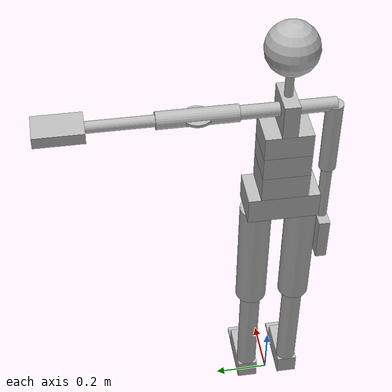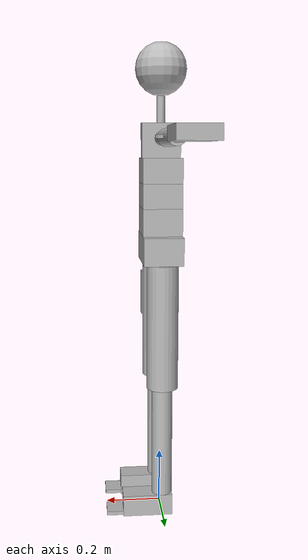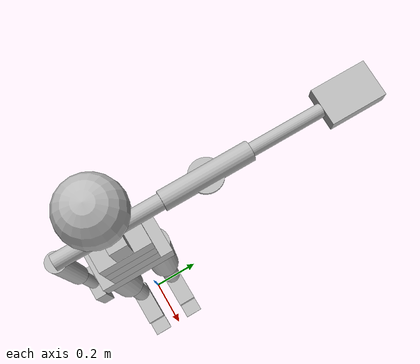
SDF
<sdf version='1.6'>
  <model name='humanSubject01_semi-fixed'>
    <pose>0 0 0.9325 0 0 0</pose>
    <!--Link base (1)-->
    <link name='Pelvis'>
      <pose frame=''>0 0 0 0 -0 0</pose>
      <inertial>
        <pose frame=''>0 0 0.049333 0 -0 0</pose>
        <mass>4.976</mass>
        <inertia>
          <ixx>0.029678</ixx>
          <ixy>0</ixy>
          <ixz>0</ixz>
          <iyy>0.011854</iyy>
          <iyz>0</iyz>
          <izz>0.033653</izz>
        </inertia>
      </inertial>

      <collision name='Pelvis_collision'>
        <pose frame=''>0 0 0.049333 0 -0 0</pose>
        <geometry>
          <box>
            <size>0.13815  0.24914  0.097469</size>
          </box>
        </geometry>
      </collision>

      <visual name='Pelvis_visual'>
        <pose frame=''>0 0 0.049333 0 -0 0</pose>
        <geometry>
          <box>
            <size>0.13815  0.24914  0.097469</size>
          </box>
        </geometry>
      </visual>
    </link>

    <!--Chain from (2) to (7)-->
    <link name='L5_f1'>
      <pose relative_to='jL5S1_rotx'>0 0 0 0 -0 0</pose>
      <inertial>
        <pose frame=''>0 0 0 0 -0 0</pose>
        <mass>0.001</mass>
        <inertia>
          <ixx>0.0003</ixx>
          <ixy>0</ixy>
          <ixz>0</ixz>
          <iyy>0.0003</iyy>
          <iyz>0</iyz>
          <izz>0.0003</izz>
        </inertia>
      </inertial>
    </link>
    <link name='L5_f2'>
      <pose relative_to='jL5S1_roty'>0 0 0 0 -0 0</pose>
      <inertial>
        <pose frame=''>0 0 0 0 -0 0</pose>
        <mass>0.001</mass>
        <inertia>
          <ixx>0.0003</ixx>
          <ixy>0</ixy>
          <ixz>0</ixz>
          <iyy>0.0003</iyy>
          <iyz>0</iyz>
          <izz>0.0003</izz>
        </inertia>
      </inertial>
    </link>
    <link name='L5'>

      <pose relative_to='jL5S1_rotz'>0 0 0 0 -0 0</pose>
      <inertial>
        <pose frame=''>0 0 0.047552 0 -0 0</pose>
        <mass>6.3444</mass>
        <inertia>
          <ixx>0.018868</ixx>
          <ixy>0</ixy>
          <ixz>0</ixz>
          <iyy>0.014872</iyy>
          <iyz>0</iyz>
          <izz>0.024177</izz>
        </inertia>
      </inertial>

      <collision name='L5_collision'>
        <pose frame=''>0 0 0.047552 0 -0 0</pose>
        <geometry>
          <box>
            <size>0.13815  0.16323   0.095104</size>
          </box>
        </geometry>
      </collision>

      <visual name='L5_visual'>
        <pose frame=''>0 0 0.047552 0 -0 0</pose>
        <geometry>
          <box>
            <size>0.13815  0.16323   0.095104</size>
          </box>
        </geometry>
      </visual>

    </link>
    <link name='L3_f1'>
      <pose relative_to='jL4L3_rotx'>0 0 0 0 -0 0</pose>
      <inertial>
        <pose frame=''>0 0 0 0 -0 0</pose>
        <mass>0.001</mass>
        <inertia>
          <ixx>0.0003</ixx>
          <ixy>0</ixy>
          <ixz>0</ixz>
          <iyy>0.0003</iyy>
          <iyz>0</iyz>
          <izz>0.0003</izz>
        </inertia>
      </inertial>
    </link>
    <link name='L3_f2'>
      <pose relative_to='jL4L3_roty'>0 0 0 0 -0 0</pose>
      <inertial>
        <pose frame=''>0 0 0 0 -0 0</pose>
        <mass>0.001</mass>
        <inertia>
          <ixx>0.0003</ixx>
          <ixy>0</ixy>
          <ixz>0</ixz>
          <iyy>0.0003</iyy>
          <iyz>0</iyz>
          <izz>0.0003</izz>
        </inertia>
      </inertial>
    </link>
    <link name='L3'>
      <pose relative_to='jL4L3_rotz'>0 0 0 0 -0 0</pose>
      <inertial>
        <pose frame=''>0 0 0.042958 0 -0 0</pose>
        <mass>6.3444</mass>
        <inertia>
          <ixx>0.017989</ixx>
          <ixy>0</ixy>
          <ixz>0</ixz>
          <iyy>0.013993</iyy>
          <iyz>0</iyz>
          <izz>0.024177</izz>
        </inertia>
      </inertial>
      <collision name='L3_collision'>
        <pose frame=''>0 0 0.042958 0 -0 0</pose>
        <geometry>
          <box>
            <size>0.13815  0.16323   0.085916</size>
          </box>
        </geometry>
      </collision>
      <visual name='L3_visual'>
        <pose frame=''>0 0 0.042958 0 -0 0</pose>
        <geometry>
          <box>
            <size>0.13815  0.16323   0.085916</size>
          </box>
        </geometry>
      </visual>
    </link>
    <link name='T12_f1'>
      <pose relative_to='jL1T12_rotx'>0 0 0 0 -0 0</pose>
      <inertial>
        <pose frame=''>0 0 0 0 -0 0</pose>
        <mass>0.001</mass>
        <inertia>
          <ixx>0.0003</ixx>
          <ixy>0</ixy>
          <ixz>0</ixz>
          <iyy>0.0003</iyy>
          <iyz>0</iyz>
          <izz>0.0003</izz>
        </inertia>
      </inertial>
    </link>
    <link name='T12_f2'>
      <pose relative_to='jL1T12_roty'>0 0 0 0 -0 0</pose>
      <inertial>
        <pose frame=''>0 0 0 0 -0 0</pose>
        <mass>0.001</mass>
        <inertia>
          <ixx>0.0003</ixx>
          <ixy>0</ixy>
          <ixz>0</ixz>
          <iyy>0.0003</iyy>
          <iyz>0</iyz>
          <izz>0.0003</izz>
        </inertia>
      </inertial>
    </link>
    <link name='T12'>
      <pose relative_to='jL1T12_rotz'>0 0 0 0 -0 0</pose>
      <inertial>
        <pose frame=''>0 0 0.042958 0 -0 0</pose>
        <mass>6.3444</mass>
        <inertia>
          <ixx>0.017989</ixx>
          <ixy>0</ixy>
          <ixz>0</ixz>
          <iyy>0.013993</iyy>
          <iyz>0</iyz>
          <izz>0.024177</izz>
        </inertia>
      </inertial>
      <collision name='T12_collision'>
        <pose frame=''>0 0 0.042958 0 -0 0</pose>
        <geometry>
          <box>
            <size>0.13815  0.16323  0.085916</size>
          </box>
        </geometry>
      </collision>
      <visual name='T12_visual'>
        <pose frame=''>0 0 0.042958 0 -0 0</pose>
        <geometry>
          <box>
            <size>0.13815  0.16323  0.085916</size>
          </box>
        </geometry>
      </visual>
    </link>
    <link name='T8_f1'>
      <pose relative_to='jT9T8_rotx'>0 0 0 0 -0 0</pose>
      <inertial>
        <pose frame=''>0 0 0 0 -0 0</pose>
        <mass>0.001</mass>
        <inertia>
          <ixx>0.0003</ixx>
          <ixy>0</ixy>
          <ixz>0</ixz>
          <iyy>0.0003</iyy>
          <iyz>0</iyz>
          <izz>0.0003</izz>
        </inertia>
      </inertial>
    </link>
    <link name='T8_f2'>
      <pose relative_to='jT9T8_roty'>0 0 0 0 -0 0</pose>
      <inertial>
        <pose frame=''>0 0 0 0 -0 0</pose>
        <mass>0.001</mass>
        <inertia>
          <ixx>0.0003</ixx>
          <ixy>0</ixy>
          <ixz>0</ixz>
          <iyy>0.0003</iyy>
          <iyz>0</iyz>
          <izz>0.0003</izz>
        </inertia>
      </inertial>
    </link>
    <link name='T8'>
      <pose relative_to='jT9T8_rotz'>0 0 0 0 -0 0</pose>
      <inertial>
        <pose frame=''>0 0 0.059874 0 -0 0</pose>
        <mass>2.488</mass>
        <inertia>
          <ixx>0.0035473</ixx>
          <ixy>0</ixy>
          <ixz>0</ixz>
          <iyy>0.0067278</iyy>
          <iyz>0</iyz>
          <izz>0.0043289</izz>
        </inertia>
      </inertial>
      <collision name='T8_collision'>
        <pose frame=''>0 0 0.059874 0 -0 0</pose>
        <geometry>
          <box>
            <size>0.13457  0.052626  0.11975</size>
          </box>
        </geometry>
      </collision>
      <visual name='T8_visual'>
        <pose frame=''>0 0 0.059874 0 -0 0</pose>
        <geometry>
          <box>
            <size>0.13457  0.052626  0.11975</size>
          </box>
        </geometry>
      </visual>
    </link>
    <link name='Neck_f1'>
      <pose relative_to='jT1C7_rotx'>0 0 0 0 -0 0</pose>
      <inertial>
        <pose frame=''>0 0 0 0 -0 0</pose>
        <mass>0.001</mass>
        <inertia>
          <ixx>0.0003</ixx>
          <ixy>0</ixy>
          <ixz>0</ixz>
          <iyy>0.0003</iyy>
          <iyz>0</iyz>
          <izz>0.0003</izz>
        </inertia>
      </inertial>
    </link>
    <link name='Neck_f2'>
      <pose relative_to='jT1C7_roty'>0 0 0 0 -0 0</pose>
      <inertial>
        <pose frame=''>0 0 0 0 -0 0</pose>
        <mass>0.001</mass>
        <inertia>
          <ixx>0.0003</ixx>
          <ixy>0</ixy>
          <ixz>0</ixz>
          <iyy>0.0003</iyy>
          <iyz>0</iyz>
          <izz>0.0003</izz>
        </inertia>
      </inertial>
    </link>
    <link name='Neck'>
      <pose relative_to='jT1C7_rotz'>0 0 0 0 -0 0</pose>
      <inertial>
        <pose frame=''>0 0 0.044626 0 -0 0</pose>
        <mass>0.7464</mass>
        <inertia>
          <ixx>0.0006461</ixx>
          <ixy>0</ixy>
          <ixz>0</ixz>
          <iyy>0.0006461</iyy>
          <iyz>0</iyz>
          <izz>0.00030124</izz>
        </inertia>
      </inertial>
      <collision name='Neck_collision'>
        <pose frame=''>0 0 0.044626 0 -0 0</pose>
        <geometry>
          <cylinder>
            <length>0.089252</length>
            <radius>0.014205</radius>
          </cylinder>
        </geometry>
      </collision>
      <visual name='Neck_visual'>
        <pose frame=''>0 0 0.044626 0 -0 0</pose>
        <geometry>
          <cylinder>
            <length>0.089252</length>
            <radius>0.014205</radius>
          </cylinder>
        </geometry>
      </visual>
    </link>
    <link name='Head_f1'>
      <pose relative_to='jC1Head_rotx'>0 0 0 0 -0 0</pose>
      <inertial>
        <pose frame=''>0 0 0 0 -0 0</pose>
        <mass>0.001</mass>
        <inertia>
          <ixx>0.0003</ixx>
          <ixy>0</ixy>
          <ixz>0</ixz>
          <iyy>0.0003</iyy>
          <iyz>0</iyz>
          <izz>0.0003</izz>
        </inertia>
      </inertial>
    </link>
    <link name='Head_f2'>
      <pose relative_to='jC1Head_roty'>0 0 0 0 -0 0</pose>
      <inertial>
        <pose frame=''>0 0 0 0 -0 0</pose>
        <mass>0.001</mass>
        <inertia>
          <ixx>0.0003</ixx>
          <ixy>0</ixy>
          <ixz>0</ixz>
          <iyy>0.0003</iyy>
          <iyz>0</iyz>
          <izz>0.0003</izz>
        </inertia>
      </inertial>
    </link>
    <link name='Head'>
      <pose relative_to='jC1Head_rotz'>0 0 0 0 -0 0</pose>
      <inertial>
        <pose frame=''>0 0 0.089005 0 -0 0</pose>
        <mass>2.2392</mass>
        <inertia>
          <ixx>0.0070955</ixx>
          <ixy>0</ixy>
          <ixz>0</ixz>
          <iyy>0.0070955</iyy>
          <iyz>0</iyz>
          <izz>0.0070955</izz>
        </inertia>
      </inertial>
      <collision name='Head_collision'>
        <pose frame=''>0 0 0.089005 0 -0 0</pose>
        <geometry>
          <sphere>
            <radius>0.089005</radius>
          </sphere>
        </geometry>
      </collision>
      <visual name='Head_visual'>
        <pose frame=''>0 0 0.089005 0 -0 0</pose>
        <geometry>
          <sphere>
            <radius>0.089005</radius>
          </sphere>
        </geometry>
      </visual>
    </link>

    <!--Chain from (8) to (11)-->
    <link name='RightShoulder_f1'>
      <pose relative_to='jRightC7Shoulder_rotx'>0 0 0 0 -0 0</pose>
      <inertial>
        <pose frame=''>0 0 0 0 -0 0</pose>
        <mass>0.001</mass>
        <inertia>
          <ixx>0.0003</ixx>
          <ixy>0</ixy>
          <ixz>0</ixz>
          <iyy>0.0003</iyy>
          <iyz>0</iyz>
          <izz>0.0003</izz>
        </inertia>
      </inertial>
    </link>
    <link name='RightShoulder_f2'>
      <pose relative_to='jRightC7Shoulder_roty'>0 0 0 0 -0 0</pose>
      <inertial>
        <pose frame=''>0 0 0 0 -0 0</pose>
        <mass>0.001</mass>
        <inertia>
          <ixx>0.0003</ixx>
          <ixy>0</ixy>
          <ixz>0</ixz>
          <iyy>0.0003</iyy>
          <iyz>0</iyz>
          <izz>0.0003</izz>
        </inertia>
      </inertial>
    </link>
    <link name='RightShoulder'>
      <pose relative_to='jRightC7Shoulder_rotz'>0 0 0 0 -0 0</pose>
      <inertial>
        <pose frame=''>0 -0.065233 0 0 -0 0</pose>
        <mass>1.9282</mass>
        <inertia>
          <ixx>0.0030029</ixx>
          <ixy>0</ixy>
          <ixz>0</ixz>
          <iyy>0.00053578</iyy>
          <iyz>0</iyz>
          <izz>0.0030029</izz>
        </inertia>
      </inertial>
      <collision name='RightShoulder_collision'>
        <pose frame=''>0 -0.065233 0 1.5708 -0 0</pose>
        <geometry>
          <cylinder>
            <length>0.13047</length>
            <radius>0.023574</radius>
          </cylinder>
        </geometry>
      </collision>
      <visual name='RightShoulder_visual'>
        <pose frame=''>0 -0.069978 0 1.5708 -0 0</pose>
        <geometry>
          <cylinder>
            <length>0.13047</length>
            <radius>0.023574</radius>
          </cylinder>
        </geometry>
      </visual>
    </link>
    <link name='RightUpperArm_f1'>
      <pose relative_to='jRightShoulder_rotx'>0 0 0 0 -0 0</pose>
      <inertial>
        <pose frame=''>0 0 0 0 -0 0</pose>
        <mass>0.001</mass>
        <inertia>
          <ixx>0.0003</ixx>
          <ixy>0</ixy>
          <ixz>0</ixz>
          <iyy>0.0003</iyy>
          <iyz>0</iyz>
          <izz>0.0003</izz>
        </inertia>
      </inertial>
    </link>
    <link name='RightUpperArm_f2'>
      <pose relative_to='jRightShoulder_roty'>0 0 0 0 -0 0</pose>
      <inertial>
        <pose frame=''>0 0 0 0 -0 0</pose>
        <mass>0.001</mass>
        <inertia>
          <ixx>0.0003</ixx>
          <ixy>0</ixy>
          <ixz>0</ixz>
          <iyy>0.0003</iyy>
          <iyz>0</iyz>
          <izz>0.0003</izz>
        </inertia>
      </inertial>
    </link>
    <link name='RightUpperArm'>
      <pose relative_to='jRightShoulder_rotz'>0 0 0 0 -0 0</pose>
      <inertial>
        <pose frame=''>0 -0.13497 0 0 -0 0</pose>
        <mass>1.866</mass>
        <inertia>
          <ixx>0.011736</ixx>
          <ixy>0</ixy>
          <ixz>0</ixz>
          <iyy>0.00080917</iyy>
          <iyz>0</iyz>
          <izz>0.011736</izz>
        </inertia>
      </inertial>
      <collision name='RightUpperArm_collision'>
        <pose frame=''>0 -0.13497 0 1.5708 -0 0</pose>
        <geometry>
          <cylinder>
            <length>0.26994</length>
            <radius>0.029449</radius>
          </cylinder>
        </geometry>
      </collision>
      <visual name='RightUpperArm_visual'>
        <pose frame=''>0 -0.13497 0 1.5708 -0 0</pose>
        <geometry>
          <cylinder>
            <length>0.26994</length>
            <radius>0.029449</radius>
          </cylinder>
        </geometry>
      </visual>
    </link>
    <link name='RightForeArm_f1'>
      <pose relative_to='jRightElbow_rotx'>0 0 0 0 -0 0</pose>
      <inertial>
        <pose frame=''>0 0 0 0 -0 0</pose>
        <mass>0.001</mass>
        <inertia>
          <ixx>0.0003</ixx>
          <ixy>0</ixy>
          <ixz>0</ixz>
          <iyy>0.0003</iyy>
          <iyz>0</iyz>
          <izz>0.0003</izz>
        </inertia>
      </inertial>
    </link>
    <link name='RightForeArm_f2'>
      <pose relative_to='jRightElbow_roty'>0 0 0 0 -0 0</pose>
      <inertial>
        <pose frame=''>0 0 0 0 -0 0</pose>
        <mass>0.001</mass>
        <inertia>
          <ixx>0.0003</ixx>
          <ixy>0</ixy>
          <ixz>0</ixz>
          <iyy>0.0003</iyy>
          <iyz>0</iyz>
          <izz>0.0003</izz>
        </inertia>
      </inertial>
    </link>
    <link name='RightForeArm'>
      <pose relative_to='jRightElbow_rotz'>0 0 0 0 -0 0</pose>
      <inertial>
        <pose frame=''>0 -0.11124 0 0 -0 0</pose>
        <mass>1.244</mass>
        <inertia>
          <ixx>0.0052508</ixx>
          <ixy>0</ixy>
          <ixz>0</ixz>
          <iyy>0.00023975</iyy>
          <iyz>0</iyz>
          <izz>0.0052508</izz>
        </inertia>
      </inertial>
      <collision name='RightForeArm_collision'>
        <pose frame=''>0 -0.11124 0 1.5708 -0 0</pose>
        <geometry>
          <cylinder>
            <length>0.22247</length>
            <radius>0.019633</radius>
          </cylinder>
        </geometry>
      </collision>
      <visual name='RightForeArm_visual'>
        <pose frame=''>0 -0.11124 0 1.5708 -0 0</pose>
        <geometry>
          <cylinder>
            <length>0.22247</length>
            <radius>0.019633</radius>
          </cylinder>
        </geometry>
      </visual>
    </link>
    <link name='RightHand_f1'>
      <pose relative_to='jRightWrist_rotx'>0 0 0 0 -0 0</pose>
      <inertial>
        <pose frame=''>0 0 0 0 -0 0</pose>
        <mass>0.001</mass>
        <inertia>
          <ixx>0.0003</ixx>
          <ixy>0</ixy>
          <ixz>0</ixz>
          <iyy>0.0003</iyy>
          <iyz>0</iyz>
          <izz>0.0003</izz>
        </inertia>
      </inertial>
    </link>
    <link name='RightHand_f2'>
      <pose relative_to='jRightWrist_roty'>0 0 0 0 -0 0</pose>
      <inertial>
        <pose frame=''>0 0 0 0 -0 0</pose>
        <mass>0.001</mass>
        <inertia>
          <ixx>0.0003</ixx>
          <ixy>0</ixy>
          <ixz>0</ixz>
          <iyy>0.0003</iyy>
          <iyz>0</iyz>
          <izz>0.0003</izz>
        </inertia>
      </inertial>
    </link>
    <link name='RightHand'>
      <pose relative_to='jRightWrist_rotz'>0 0 0 0 -0 0</pose>
      <inertial>
        <pose frame=''>0 -0.083588 0 0 -0 0</pose>
        <mass>0.3732</mass>
        <inertia>
          <ixx>0.00091713</ixx>
          <ixy>0</ixy>
          <ixz>0</ixz>
          <iyy>0.00043425</iyy>
          <iyz>0</iyz>
          <izz>0.0012555</izz>
        </inertia>
      </inertial>
      <collision name='RightHand_collision'>
        <pose frame=''>0 -0.083588 0 0 -0 0</pose>
        <geometry>
          <box>
            <size>0.11145  0.16718  0.039266</size>
          </box>
        </geometry>
      </collision>
      <visual name='RightHand_visual'>
        <pose frame=''>0 -0.083588 0 0 -0 0</pose>
        <geometry>
          <box>
            <size>0.11145  0.16718  0.039266</size>
          </box>
        </geometry>
      </visual>
    </link>

    <!--Chain from (12) to (15)-->
    <link name='LeftShoulder_f1'>
      <pose relative_to='jLeftC7Shoulder_rotx'>0 0 0 0 -0 0</pose>
      <inertial>
        <pose frame=''>0 0 0 0 -0 0</pose>
        <mass>0.001</mass>
        <inertia>
          <ixx>0.0003</ixx>
          <ixy>0</ixy>
          <ixz>0</ixz>
          <iyy>0.0003</iyy>
          <iyz>0</iyz>
          <izz>0.0003</izz>
        </inertia>
      </inertial>
    </link>
    <link name='LeftShoulder_f2'>
      <pose relative_to='jLeftC7Shoulder_roty'>0 0 0 0 -0 0</pose>
      <inertial>
        <pose frame=''>0 0 0 0 -0 0</pose>
        <mass>0.001</mass>
        <inertia>
          <ixx>0.0003</ixx>
          <ixy>0</ixy>
          <ixz>0</ixz>
          <iyy>0.0003</iyy>
          <iyz>0</iyz>
          <izz>0.0003</izz>
        </inertia>
      </inertial>
    </link>
    <link name='LeftShoulder'>
      <pose relative_to='jLeftC7Shoulder_rotz'>0 0 0 0 -0 0</pose>
      <inertial>
        <pose frame=''>0 0.065233 0 0 -0 0</pose>
        <mass>1.9282</mass>
        <inertia>
          <ixx>0.0030029</ixx>
          <ixy>0</ixy>
          <ixz>0</ixz>
          <iyy>0.00053578</iyy>
          <iyz>0</iyz>
          <izz>0.0030029</izz>
        </inertia>
      </inertial>
      <collision name='LeftShoulder_collision'>
        <pose frame=''>0 0.065233 0 1.5708 -0 0</pose>
        <geometry>
          <cylinder>
            <length>0.13047</length>
            <radius>0.023574</radius>
          </cylinder>
        </geometry>
      </collision>
      <visual name='LeftShoulder_visual'>
        <pose frame=''>0 0.065233 0 1.5708 -0 0</pose>
        <geometry>
          <cylinder>
            <length>0.13047</length>
            <radius>0.023574</radius>
          </cylinder>
        </geometry>
      </visual>
    </link>
    <link name='LeftUpperArm_f1'>
      <pose relative_to='jLeftShoulder_rotx'>0 0 0 0 -0 0</pose>
      <inertial>
        <pose frame=''>0 0 0 0 -0 0</pose>
        <mass>0.001</mass>
        <inertia>
          <ixx>0.0003</ixx>
          <ixy>0</ixy>
          <ixz>0</ixz>
          <iyy>0.0003</iyy>
          <iyz>0</iyz>
          <izz>0.0003</izz>
        </inertia>
      </inertial>
    </link>
    <link name='LeftUpperArm_f2'>
      <pose relative_to='jLeftShoulder_roty'>0 0 0 0 0 0</pose>
      <inertial>
        <pose frame=''>0 0 0 0 -0 0</pose>
        <mass>0.001</mass>
        <inertia>
          <ixx>0.0003</ixx>
          <ixy>0</ixy>
          <ixz>0</ixz>
          <iyy>0.0003</iyy>
          <iyz>0</iyz>
          <izz>0.0003</izz>
        </inertia>
      </inertial>
    </link>
    <link name='LeftUpperArm'>
      <pose relative_to='jLeftShoulder_rotz'>0 0 0 0 0 0</pose>
      <inertial>
        <pose frame=''>0 0.13497 0 0 -0 0</pose>
        <mass>1.866</mass>
        <inertia>
          <ixx>0.011736</ixx>
          <ixy>0</ixy>
          <ixz>0</ixz>
          <iyy>0.00080917</iyy>
          <iyz>0</iyz>
          <izz>0.011736</izz>
        </inertia>
      </inertial>
      <collision name='LeftUpperArm_collision'>
        <pose frame=''>0 0.13497 0 1.5708 -0 0</pose>
        <geometry>
          <cylinder>
            <length>0.26994</length>
            <radius>0.029449</radius>
          </cylinder>
        </geometry>
      </collision>
      <visual name='LeftUpperArm_visual'>
        <pose frame=''>0 0.13497 0 1.5708 -0 0</pose>
        <geometry>
          <cylinder>
            <length>0.26994</length>
            <radius>0.029449</radius>
          </cylinder>
        </geometry>
      </visual>
    </link>
    <link name='LeftForeArm_f1'>
      <pose relative_to='jLeftElbow_rotx'>0 0 0 0 -0 0</pose>
      <inertial>
        <pose frame=''>0 0 0 0 -0 0</pose>
        <mass>0.001</mass>
        <inertia>
          <ixx>0.0003</ixx>
          <ixy>0</ixy>
          <ixz>0</ixz>
          <iyy>0.0003</iyy>
          <iyz>0</iyz>
          <izz>0.0003</izz>
        </inertia>
      </inertial>
    </link>
    <link name='LeftForeArm_f2'>
      <pose relative_to='jLeftElbow_roty'>0 0 0 0 -0 0</pose>
      <inertial>
        <pose frame=''>0 0 0 0 -0 0</pose>
        <mass>0.001</mass>
        <inertia>
          <ixx>0.0003</ixx>
          <ixy>0</ixy>
          <ixz>0</ixz>
          <iyy>0.0003</iyy>
          <iyz>0</iyz>
          <izz>0.0003</izz>
        </inertia>
      </inertial>
    </link>
    <link name='LeftForeArm'>
      <pose relative_to='jLeftElbow_rotz'>0 0 0 0 -0 0</pose>
      <inertial>
        <pose frame=''>0 0.11124 0 0 -0 0</pose>
        <mass>1.244</mass>
        <inertia>
          <ixx>0.0052508</ixx>
          <ixy>0</ixy>
          <ixz>0</ixz>
          <iyy>0.00023975</iyy>
          <iyz>0</iyz>
          <izz>0.0052508</izz>
        </inertia>
      </inertial>
      <collision name='LeftForeArm_collision'>
        <pose frame=''>0 0.11124 0 1.5708 -0 0</pose>
        <geometry>
          <cylinder>
            <length>0.22247</length>
            <radius>0.019633</radius>
          </cylinder>
        </geometry>
      </collision>
      <visual name='LeftForeArm_visual'>
        <pose frame=''>0 0.11124 0 1.5708 -0 0</pose>
        <geometry>
          <cylinder>
            <length>0.22247</length>
            <radius>0.019633</radius>
          </cylinder>
        </geometry>
      </visual>
    </link>
    <link name='LeftHand_f1'>
      <pose relative_to='jLeftWrist_rotx'>0 0 0 0 -0 0</pose>
      <inertial>
        <pose frame=''>0 0 0 0 -0 0</pose>
        <mass>0.001</mass>
        <inertia>
          <ixx>0.0003</ixx>
          <ixy>0</ixy>
          <ixz>0</ixz>
          <iyy>0.0003</iyy>
          <iyz>0</iyz>
          <izz>0.0003</izz>
        </inertia>
      </inertial>
    </link>
    <link name='LeftHand_f2'>
      <pose relative_to='jLeftWrist_roty'>0 0 0 0 -0 0</pose>
      <inertial>
        <pose frame=''>0 0 0 0 -0 0</pose>
        <mass>0.001</mass>
        <inertia>
          <ixx>0.0003</ixx>
          <ixy>0</ixy>
          <ixz>0</ixz>
          <iyy>0.0003</iyy>
          <iyz>0</iyz>
          <izz>0.0003</izz>
        </inertia>
      </inertial>
    </link>
    <link name='LeftHand'>
      <pose relative_to='jLeftWrist_rotz'>0 0 0 0 -0 0</pose>
      <inertial>
        <pose frame=''>0 0.083588 0 0 -0 0</pose>
        <mass>0.3732</mass>
        <inertia>
          <ixx>0.00091713</ixx>
          <ixy>0</ixy>
          <ixz>0</ixz>
          <iyy>0.00043425</iyy>
          <iyz>0</iyz>
          <izz>0.0012555</izz>
        </inertia>
      </inertial>
      <collision name='LeftHand_collision'>
        <pose frame=''>0 0.083588 0 0 -0 0</pose>
        <geometry>
          <box>
            <size>0.11145  0.16718  0.039266</size>
          </box>
        </geometry>
      </collision>
      <visual name='LeftHand_visual'>
        <pose frame=''>0 0.083588 0 0 -0 0</pose>
        <geometry>
          <box>
            <size>0.11145  0.16718  0.039266</size>
          </box>
        </geometry>
      </visual>
    </link>

    <!--Chain from (16) to (19)-->
    <link name='RightUpperLeg_f1'>
      <pose relative_to='jRightHip_rotx'>0 0 0 0 -0 0</pose>
      <inertial>
        <pose frame=''>0 0 0 0 -0 0</pose>
        <mass>0.001</mass>
        <inertia>
          <ixx>0.0003</ixx>
          <ixy>0</ixy>
          <ixz>0</ixz>
          <iyy>0.0003</iyy>
          <iyz>0</iyz>
          <izz>0.0003</izz>
        </inertia>
      </inertial>
    </link>
    <link name='RightUpperLeg_f2'>
      <pose relative_to='jRightHip_roty'>0 0 0 0 -0 0</pose>
      <inertial>
        <pose frame=''>0 0 0 0 -0 0</pose>
        <mass>0.001</mass>
        <inertia>
          <ixx>0.0003</ixx>
          <ixy>0</ixy>
          <ixz>0</ixz>
          <iyy>0.0003</iyy>
          <iyz>0</iyz>
          <izz>0.0003</izz>
        </inertia>
      </inertial>
    </link>
    <link name='RightUpperLeg'>
      <pose relative_to='jRightHip_rotz'>0 0 0 0 -0 0</pose>
      <inertial>
        <pose frame=''>0 0 -0.22449 0 -0 0</pose>
        <mass>7.775</mass>
        <inertia>
          <ixx>0.13681</ixx>
          <ixy>0</ixy>
          <ixz>0</ixz>
          <iyy>0.13681</iyy>
          <iyz>0</iyz>
          <izz>0.01241</izz>
        </inertia>
      </inertial>
      <collision name='RightUpperLeg_collision'>
        <pose frame=''>0 0 -0.22449 0 -0 0</pose>
        <geometry>
          <cylinder>
            <length>0.44898</length>
            <radius>0.0565</radius>
          </cylinder>
        </geometry>
      </collision>
      <visual name='RightUpperLeg_visual'>
        <pose frame=''>0 0 -0.22449 0 -0 0</pose>
        <geometry>
          <cylinder>
            <length>0.44898</length>
            <radius>0.0565</radius>
          </cylinder>
        </geometry>
      </visual>
    </link>
    <link name='RightLowerLeg_f1'>
      <pose relative_to='jRightKnee_rotx'>0 0 0 0 -0 0</pose>
      <inertial>
        <pose frame=''>0 0 0 0 -0 0</pose>
        <mass>0.001</mass>
        <inertia>
          <ixx>0.0003</ixx>
          <ixy>0</ixy>
          <ixz>0</ixz>
          <iyy>0.0003</iyy>
          <iyz>0</iyz>
          <izz>0.0003</izz>
        </inertia>
      </inertial>
    </link>
    <link name='RightLowerLeg_f2'>
      <pose relative_to='jRightKnee_roty'>0 0 0 0 -0 0</pose>
      <inertial>
        <pose frame=''>0 0 0 0 -0 0</pose>
        <mass>0.001</mass>
        <inertia>
          <ixx>0.0003</ixx>
          <ixy>0</ixy>
          <ixz>0</ixz>
          <iyy>0.0003</iyy>
          <iyz>0</iyz>
          <izz>0.0003</izz>
        </inertia>
      </inertial>
    </link>
    <link name='RightLowerLeg'>
      <pose relative_to='jRightKnee_rotz'>0 0 0 0 -0 0</pose>
      <inertial>
        <pose frame=''>0 0 -0.20304 0 -0 0</pose>
        <mass>2.2703</mass>
        <inertia>
          <ixx>0.031992</ixx>
          <ixy>0</ixy>
          <ixz>0</ixz>
          <iyy>0.031992</iyy>
          <iyz>0</iyz>
          <izz>0.0015867</izz>
        </inertia>
      </inertial>
      <collision name='RightLowerLeg_collision'>
        <pose frame=''>0 0 -0.20304 0 -0 0</pose>
        <geometry>
          <cylinder>
            <length>0.40608</length>
            <radius>0.037388</radius>
          </cylinder>
        </geometry>
      </collision>
      <visual name='RightLowerLeg_visual'>
        <pose frame=''>0 0 -0.20304 0 -0 0</pose>
        <geometry>
          <cylinder>
            <length>0.40608</length>
            <radius>0.037388</radius>
          </cylinder>
        </geometry>
      </visual>
    </link>
    <link name='RightFoot_f1'>
      <pose relative_to='jRightAnkle_rotx'>0 0 0 0 -0 0</pose>
      <inertial>
        <pose frame=''>0 0 0 0 -0 0</pose>
        <mass>0.001</mass>
        <inertia>
          <ixx>0.0003</ixx>
          <ixy>0</ixy>
          <ixz>0</ixz>
          <iyy>0.0003</iyy>
          <iyz>0</iyz>
          <izz>0.0003</izz>
        </inertia>
      </inertial>
    </link>
    <link name='RightFoot_f2'>
      <pose relative_to='jRightAnkle_roty'>0 0 0 0 -0 0</pose>
      <inertial>
        <pose frame=''>0 0 0 0 -0 0</pose>
        <mass>0.001</mass>
        <inertia>
          <ixx>0.0003</ixx>
          <ixy>0</ixy>
          <ixz>0</ixz>
          <iyy>0.0003</iyy>
          <iyz>0</iyz>
          <izz>0.0003</izz>
        </inertia>
      </inertial>
    </link>
    <link name='RightFoot'>
      <pose relative_to='jRightAnkle_rotz'>0 0 0 0 -0 0</pose>
      <inertial>
        <pose frame=''>0.054652 0 -0.039254 0 -0 0</pose>
        <mass>0.8086</mass>
        <inertia>
          <ixx>0.0011257</ixx>
          <ixy>0</ixy>
          <ixz>0</ixz>
          <iyy>0.0033102</iyy>
          <iyz>0</iyz>
          <izz>0.0029493</izz>
        </inertia>
      </inertial>
      <collision name='RightFoot_collision'>
        <pose frame=''>0.054652 0 -0.039254 0 -0 0</pose>
        <geometry>
          <box>
            <size>0.17983  0.074775  0.078509</size>
          </box>
        </geometry>
        <max_contacts>4</max_contacts>
        <surface>
          <contact>
            <ode>
              <soft_erp>0.2</soft_erp>
              <soft_cfm>0</soft_cfm>
              <kp>18000000</kp>
              <kd>100</kd>
              <max_vel>100</max_vel>
              <min_depth>0.0001</min_depth>
            </ode>
          </contact>
          <friction>
            <ode>
              <mu>10</mu>
              <mu2>10</mu2>
              <fdir1>0 0 0</fdir1>
              <slip1>0</slip1>
              <slip2>0</slip2>
            </ode>
          </friction>
          <bounce>
            <restitution_coefficient>0</restitution_coefficient>
            <threshold>100000</threshold>
          </bounce>
        </surface>
      </collision>
      <visual name='RightFoot_visual'>
        <pose frame=''>0.054652 0 -0.039254 0 -0 0</pose>
        <geometry>
          <box>
            <size>0.17983  0.074775  0.078509</size>
          </box>
        </geometry>
      </visual>
    </link>
    <link name='RightToe_f1'>
      <pose relative_to='jRightBallFoot_rotx'>0 0 0 0 -0 0</pose>
      <inertial>
        <pose frame=''>0 0 0 0 -0 0</pose>
        <mass>0.001</mass>
        <inertia>
          <ixx>0.0003</ixx>
          <ixy>0</ixy>
          <ixz>0</ixz>
          <iyy>0.0003</iyy>
          <iyz>0</iyz>
          <izz>0.0003</izz>
        </inertia>
      </inertial>
    </link>
    <link name='RightToe_f2'>
      <pose relative_to='jRightBallFoot_roty'>0 0 0 0 -0 0</pose>
      <inertial>
        <pose frame=''>0 0 0 0 -0 0</pose>
        <mass>0.001</mass>
        <inertia>
          <ixx>0.0003</ixx>
          <ixy>0</ixy>
          <ixz>0</ixz>
          <iyy>0.0003</iyy>
          <iyz>0</iyz>
          <izz>0.0003</izz>
        </inertia>
      </inertial>
    </link>
    <link name='RightToe'>
      <pose relative_to='jRightBallFoot_rotz'>0 0 0 0 -0 0</pose>
      <inertial>
        <pose frame=''>0.030086 0 0 0 -0 0</pose>
        <mass>0.0933</mass>
        <inertia>
          <ixx>4.5038e-05</ixx>
          <ixy>0</ixy>
          <ixz>0</ixz>
          <iyy>2.9717e-05</iyy>
          <iyz>0</iyz>
          <izz>7.1624e-05</izz>
        </inertia>
      </inertial>
      <collision name='RightToe_collision'>
        <pose frame=''>0.030086 0 0 0 -0 0</pose>
        <geometry>
          <box>
            <size>0.060173  0.074775  0.014191</size>
          </box>
        </geometry>
      </collision>
      <visual name='RightToe_visual'>
        <pose frame=''>0.030086 0 0 0 -0 0</pose>
        <geometry>
          <box>
            <size>0.060173  0.074775  0.014191</size>
          </box>
        </geometry>
      </visual>
    </link>

    <!--Chain from (20) to (23)-->
    <link name='LeftUpperLeg_f1'>
      <pose relative_to='jLeftHip_rotx'>0 0 0 0 -0 0</pose>
      <inertial>
        <pose frame=''>0 0 0 0 -0 0</pose>
        <mass>0.001</mass>
        <inertia>
          <ixx>0.0003</ixx>
          <ixy>0</ixy>
          <ixz>0</ixz>
          <iyy>0.0003</iyy>
          <iyz>0</iyz>
          <izz>0.0003</izz>
        </inertia>
      </inertial>
    </link>
    <link name='LeftUpperLeg_f2'>
      <pose relative_to='jLeftHip_roty'>0 0 0 0 -0 0</pose>
      <inertial>
        <pose frame=''>0 0 0 0 -0 0</pose>
        <mass>0.001</mass>
        <inertia>
          <ixx>0.0003</ixx>
          <ixy>0</ixy>
          <ixz>0</ixz>
          <iyy>0.0003</iyy>
          <iyz>0</iyz>
          <izz>0.0003</izz>
        </inertia>
      </inertial>
    </link>
    <link name='LeftUpperLeg'>
      <pose relative_to='jLeftHip_rotz'>0 0 0 0 -0 0</pose>
      <inertial>
        <pose frame=''>0 0 -0.22449 0 -0 0</pose>
        <mass>7.775</mass>
        <inertia>
          <ixx>0.13681</ixx>
          <ixy>0</ixy>
          <ixz>0</ixz>
          <iyy>0.13681</iyy>
          <iyz>0</iyz>
          <izz>0.01241</izz>
        </inertia>
      </inertial>
      <collision name='LeftUpperLeg_collision'>
        <pose frame=''>0 0 -0.22449 0 -0 0</pose>
        <geometry>
          <cylinder>
            <length>0.44898</length>
            <radius>0.0565</radius>
          </cylinder>
        </geometry>
      </collision>
      <visual name='LeftUpperLeg_visual'>
        <pose frame=''>0 0 -0.22449 0 -0 0</pose>
        <geometry>
          <cylinder>
            <length>0.44898</length>
            <radius>0.0565</radius>
          </cylinder>
        </geometry>
      </visual>
    </link>
    <link name='LeftLowerLeg_f1'>
      <pose relative_to='jLeftKnee_rotx'>0 0 0 0 -0 0</pose>
      <inertial>
        <pose frame=''>0 0 0 0 -0 0</pose>
        <mass>0.001</mass>
        <inertia>
          <ixx>0.0003</ixx>
          <ixy>0</ixy>
          <ixz>0</ixz>
          <iyy>0.0003</iyy>
          <iyz>0</iyz>
          <izz>0.0003</izz>
        </inertia>
      </inertial>
    </link>
    <link name='LeftLowerLeg_f2'>
      <pose relative_to='jLeftKnee_roty'>0 0 0 0 -0 0</pose>
      <inertial>
        <pose frame=''>0 0 0 0 -0 0</pose>
        <mass>0.001</mass>
        <inertia>
          <ixx>0.0003</ixx>
          <ixy>0</ixy>
          <ixz>0</ixz>
          <iyy>0.0003</iyy>
          <iyz>0</iyz>
          <izz>0.0003</izz>
        </inertia>
      </inertial>
    </link>
    <link name='LeftLowerLeg'>
      <pose relative_to='jLeftKnee_rotz'>0 0 0 0 -0 0</pose>
      <inertial>
        <pose frame=''>0 0 -0.20304 0 -0 0</pose>
        <mass>2.2703</mass>
        <inertia>
          <ixx>0.031992</ixx>
          <ixy>0</ixy>
          <ixz>0</ixz>
          <iyy>0.031992</iyy>
          <iyz>0</iyz>
          <izz>0.0015867</izz>
        </inertia>
      </inertial>
      <collision name='LeftLowerLeg_collision'>
        <pose frame=''>0 0 -0.20304 0 -0 0</pose>
        <geometry>
          <cylinder>
            <length>0.40608</length>
            <radius>0.037388</radius>
          </cylinder>
        </geometry>
      </collision>
      <visual name='LeftLowerLeg_visual'>
        <pose frame=''>0 0 -0.20304 0 -0 0</pose>
        <geometry>
          <cylinder>
            <length>0.40608</length>
            <radius>0.037388</radius>
          </cylinder>
        </geometry>
      </visual>
    </link>
    <link name='LeftFoot_f1'>
      <pose relative_to='jLeftAnkle_rotx'>0 0 0 0 -0 0</pose>
      <inertial>
        <pose frame=''>0 0 0 0 -0 0</pose>
        <mass>0.001</mass>
        <inertia>
          <ixx>0.0003</ixx>
          <ixy>0</ixy>
          <ixz>0</ixz>
          <iyy>0.0003</iyy>
          <iyz>0</iyz>
          <izz>0.0003</izz>
        </inertia>
      </inertial>
    </link>
    <link name='LeftFoot_f2'>
      <pose relative_to='jLeftAnkle_roty'>0 0 0 0 -0 0</pose>
      <inertial>
        <pose frame=''>0 0 0 0 -0 0</pose>
        <mass>0.001</mass>
        <inertia>
          <ixx>0.0003</ixx>
          <ixy>0</ixy>
          <ixz>0</ixz>
          <iyy>0.0003</iyy>
          <iyz>0</iyz>
          <izz>0.0003</izz>
        </inertia>
      </inertial>
    </link>
    <link name='LeftFoot'>
      <pose relative_to='jLeftAnkle_rotz'>0 0 0 0 -0 0</pose>
      <inertial>
        <pose frame=''>0.054652 0 -0.039254 0 -0 0</pose>
        <mass>0.8086</mass>
        <inertia>
          <ixx>0.00079209</ixx>
          <ixy>0</ixy>
          <ixz>0</ixz>
          <iyy>0.0025944</iyy>
          <iyz>0</iyz>
          <izz>0.0025558</izz>
        </inertia>
      </inertial>
      <collision name='LeftFoot_collision'>
        <pose frame=''>0.054652 0 -0.039254 0 -0 0</pose>
        <geometry>
          <box>
            <size>0.17983  0.074775  0.078509</size>
          </box>
        </geometry>
        <max_contacts>4</max_contacts>
        <surface>
          <contact>
            <ode>
              <soft_erp>0.2</soft_erp>
              <soft_cfm>0</soft_cfm>
              <kp>18000000</kp>
              <kd>100</kd>
              <max_vel>100</max_vel>
              <min_depth>0.0001</min_depth>
            </ode>
          </contact>
          <friction>
            <ode>
              <mu>10</mu>
              <mu2>10</mu2>
              <fdir1>0 0 0</fdir1>
              <slip1>0</slip1>
              <slip2>0</slip2>
            </ode>
          </friction>
          <bounce>
            <restitution_coefficient>0</restitution_coefficient>
            <threshold>100000</threshold>
          </bounce>
        </surface>
      </collision>
      <visual name='LeftFoot_visual'>
        <pose frame=''>0.054652 0 -0.039254 0 -0 0</pose>
        <geometry>
          <box>
            <size>0.17983  0.074775  0.078509</size>
          </box>
        </geometry>
      </visual>
    </link>
    <link name='LeftToe_f1'>
      <pose relative_to='jLeftBallFoot_rotx'>0 0 0 0 -0 0</pose>
      <inertial>
        <pose frame=''>0 0 0 0 -0 0</pose>
        <mass>0.001</mass>
        <inertia>
          <ixx>0.0003</ixx>
          <ixy>0</ixy>
          <ixz>0</ixz>
          <iyy>0.0003</iyy>
          <iyz>0</iyz>
          <izz>0.0003</izz>
        </inertia>
      </inertial>
    </link>
    <link name='LeftToe_f2'>
      <pose relative_to='jLeftBallFoot_roty'>0 0 0 0 -0 0</pose>
      <inertial>
        <pose frame=''>0 0 0 0 -0 0</pose>
        <mass>0.001</mass>
        <inertia>
          <ixx>0.0003</ixx>
          <ixy>0</ixy>
          <ixz>0</ixz>
          <iyy>0.0003</iyy>
          <iyz>0</iyz>
          <izz>0.0003</izz>
        </inertia>
      </inertial>
    </link>
    <link name='LeftToe'>
      <pose relative_to='jLeftBallFoot_rotz'>0 0 0 0 -0 0</pose>
      <inertial>
        <pose frame=''>0.030086 0 0 0 -0 0</pose>
        <mass>0.0933</mass>
        <inertia>
          <ixx>4.5038e-05</ixx>
          <ixy>0</ixy>
          <ixz>0</ixz>
          <iyy>2.9717e-05</iyy>
          <iyz>0</iyz>
          <izz>7.1624e-05</izz>
        </inertia>
      </inertial>
      <collision name='LeftToe_collision'>
        <pose frame=''>0.030086 0 0 0 -0 0</pose>
        <geometry>
          <box>
            <size>0.060173  0.074775  0.014191</size>
          </box>
        </geometry>
      </collision>
      <visual name='LeftToe_visual'>
        <pose frame=''>0.030086 0 0 0 -0 0</pose>
        <geometry>
          <box>
            <size>0.060173  0.074775  0.014191</size>
          </box>
        </geometry>
      </visual>
    </link>

    <!--JOINTS-->
    <!--Chain from (2) to (7)-->
    <joint name='jL5S1_rotx' type='fixed'>
      <pose relative_to='Pelvis'>-0.000206 0 0.098478 0 -0 0</pose>
      <child>L5_f1</child>
      <parent>Pelvis</parent>
      <axis>
        <xyz>1 0 0</xyz>
        <limit>
          <lower>-10.0</lower>
          <upper>10.0</upper>
          <effort>30</effort>
          <velocity>1</velocity>
        </limit>
        <dynamics>
          <damping>3</damping>
          <friction>0</friction>
          <spring_reference>0</spring_reference>
          <spring_stiffness>0</spring_stiffness>
        </dynamics>
        <use_parent_model_frame>1</use_parent_model_frame>
      </axis>
    </joint>
    <joint name='jL5S1_roty' type='fixed'>
      <pose relative_to='L5_f1'>0 0 0 0 -0 0</pose>
      <child>L5_f2</child>
      <parent>L5_f1</parent>
      <axis>
        <xyz>0 1 0</xyz>
        <limit>
          <lower>-10.0</lower>
          <upper>10.0</upper>
          <effort>30</effort>
          <velocity>1</velocity>
        </limit>
        <dynamics>
          <damping>3</damping>
          <friction>0</friction>
          <spring_reference>0</spring_reference>
          <spring_stiffness>0</spring_stiffness>
        </dynamics>
        <use_parent_model_frame>1</use_parent_model_frame>
      </axis>
    </joint>
    <joint name='jL5S1_rotz' type='fixed'>
      <pose relative_to='L5_f2'>0 0 0 0 -0 0</pose>
      <child>L5</child>
      <parent>L5_f2</parent>
      <axis>
        <xyz>0 0 1</xyz>
        <limit>
          <lower>-10.0</lower>
          <upper>10.0</upper>
          <effort>30</effort>
          <velocity>1</velocity>
        </limit>
        <dynamics>
          <damping>3</damping>
          <friction>0</friction>
          <spring_reference>0</spring_reference>
          <spring_stiffness>0</spring_stiffness>
        </dynamics>
        <use_parent_model_frame>1</use_parent_model_frame>
      </axis>
    </joint>
    <joint name='jL4L3_rotx' type='revolute'>
      <pose relative_to='L5'>0.000374 0 0.095104 0 -0 0</pose>
      <child>L3_f1</child>
      <parent>L5</parent>
      <axis>
        <xyz>1 0 0</xyz>
        <limit>
          <lower>-10.0</lower>
          <upper>10.0</upper>
          <effort>30</effort>
          <velocity>1</velocity>
        </limit>
        <dynamics>
          <damping>3</damping>
          <friction>0</friction>
          <spring_reference>0</spring_reference>
          <spring_stiffness>0</spring_stiffness>
        </dynamics>
        <use_parent_model_frame>1</use_parent_model_frame>
      </axis>
    </joint>
    <joint name='jL4L3_roty' type='revolute'>
      <pose relative_to='L3_f1'>0 0 0 0 -0 0</pose>
      <child>L3_f2</child>
      <parent>L3_f1</parent>
      <axis>
        <xyz>0 1 0</xyz>
        <limit>
          <lower>-10.0</lower>
          <upper>10.0</upper>
          <effort>30</effort>
          <velocity>1</velocity>
        </limit>
        <dynamics>
          <damping>3</damping>
          <friction>0</friction>
          <spring_reference>0</spring_reference>
          <spring_stiffness>0</spring_stiffness>
        </dynamics>
        <use_parent_model_frame>1</use_parent_model_frame>
      </axis>
    </joint>
    <joint name='jL4L3_rotz' type='revolute'>
      <pose relative_to='L3_f2'>0 0 0 0 -0 0</pose>
      <child>L3</child>
      <parent>L3_f2</parent>
      <axis>
        <xyz>0 0 1</xyz>
        <limit>
          <lower>-10.0</lower>
          <upper>10.0</upper>
          <effort>30</effort>
          <velocity>1</velocity>
        </limit>
        <dynamics>
          <damping>3</damping>
          <friction>0</friction>
          <spring_reference>0</spring_reference>
          <spring_stiffness>0</spring_stiffness>
        </dynamics>
        <use_parent_model_frame>1</use_parent_model_frame>
      </axis>
    </joint>
    <joint name='jL1T12_rotx' type='revolute'>
      <pose relative_to='L3'>0 0 0.085916 0 -0 0</pose>
      <child>T12_f1</child>
      <parent>L3</parent>
      <axis>
        <xyz>1 0 0</xyz>
        <limit>
          <lower>-10.0</lower>
          <upper>10.0</upper>
          <effort>30</effort>
          <velocity>1</velocity>
        </limit>
        <dynamics>
          <damping>3</damping>
          <friction>0</friction>
          <spring_reference>0</spring_reference>
          <spring_stiffness>0</spring_stiffness>
        </dynamics>
        <use_parent_model_frame>1</use_parent_model_frame>
      </axis>
    </joint>
    <joint name='jL1T12_roty' type='revolute'>
      <pose relative_to='T12_f1'>0 0 0 0 -0 0</pose>
      <child>T12_f2</child>
      <parent>T12_f1</parent>
      <axis>
        <xyz>0 1 0</xyz>
        <limit>
          <lower>-10.0</lower>
          <upper>10.0</upper>
          <effort>30</effort>
          <velocity>1</velocity>
        </limit>
        <dynamics>
          <damping>3</damping>
          <friction>0</friction>
          <spring_reference>0</spring_reference>
          <spring_stiffness>0</spring_stiffness>
        </dynamics>
        <use_parent_model_frame>1</use_parent_model_frame>
      </axis>
    </joint>
    <joint name='jL1T12_rotz' type='revolute'>
      <pose relative_to='T12_f2'>0 0 0 0 -0 0</pose>
      <child>T12</child>
      <parent>T12_f2</parent>
      <axis>
        <xyz>0 0 1</xyz>
        <limit>
          <lower>-10.0</lower>
          <upper>10.0</upper>
          <effort>30</effort>
          <velocity>1</velocity>
        </limit>
        <dynamics>
          <damping>3</damping>
          <friction>0</friction>
          <spring_reference>0</spring_reference>
          <spring_stiffness>0</spring_stiffness>
        </dynamics>
        <use_parent_model_frame>1</use_parent_model_frame>
      </axis>
    </joint>
    <joint name='jT9T8_rotx' type='revolute'>
      <pose relative_to='T12'>0 0 0.085916 0 -0 0</pose>
      <child>T8_f1</child>
      <parent>T12</parent>
      <axis>
        <xyz>1 0 0</xyz>
        <limit>
          <lower>-10.0</lower>
          <upper>10.0</upper>
          <effort>30</effort>
          <velocity>1</velocity>
        </limit>
        <dynamics>
          <damping>3</damping>
          <friction>0</friction>
          <spring_reference>0</spring_reference>
          <spring_stiffness>0</spring_stiffness>
        </dynamics>
        <use_parent_model_frame>1</use_parent_model_frame>
      </axis>
    </joint>
    <joint name='jT9T8_roty' type='revolute'>
      <pose relative_to='T8_f1'>0 0 0 0 -0 0</pose>
      <child>T8_f2</child>
      <parent>T8_f1</parent>
      <axis>
        <xyz>0 1 0</xyz>
        <limit>
          <lower>-10.0</lower>
          <upper>10.0</upper>
          <effort>30</effort>
          <velocity>1</velocity>
        </limit>
        <dynamics>
          <damping>3</damping>
          <friction>0</friction>
          <spring_reference>0</spring_reference>
          <spring_stiffness>0</spring_stiffness>
        </dynamics>
        <use_parent_model_frame>1</use_parent_model_frame>
      </axis>
    </joint>
    <joint name='jT9T8_rotz' type='revolute'>
      <pose relative_to='T8_f2'>0 0 0 0 -0 0</pose>
      <child>T8</child>
      <parent>T8_f2</parent>
      <axis>
        <xyz>0 0 1</xyz>
        <limit>
          <lower>-10.0</lower>
          <upper>10.0</upper>
          <effort>30</effort>
          <velocity>1</velocity>
        </limit>
        <dynamics>
          <damping>3</damping>
          <friction>0</friction>
          <spring_reference>0</spring_reference>
          <spring_stiffness>0</spring_stiffness>
        </dynamics>
        <use_parent_model_frame>1</use_parent_model_frame>
      </axis>
    </joint>
    <joint name='jT1C7_rotx' type='fixed'>
      <pose relative_to='T8'>0 0 0.11975 0 -0 0</pose>
      <child>Neck_f1</child>
      <parent>T8</parent>
      <axis>
        <xyz>1 0 0</xyz>
        <limit>
          <lower>-10.0</lower>
          <upper>10.0</upper>
          <effort>30</effort>
          <velocity>1</velocity>
        </limit>
        <dynamics>
          <damping>3</damping>
          <friction>0</friction>
          <spring_reference>0</spring_reference>
          <spring_stiffness>0</spring_stiffness>
        </dynamics>
        <use_parent_model_frame>1</use_parent_model_frame>
      </axis>
    </joint>
    <joint name='jT1C7_roty' type='fixed'>
      <pose relative_to='Neck_f1'>0 0 0 0 -0 0</pose>
      <child>Neck_f2</child>
      <parent>Neck_f1</parent>
      <axis>
        <xyz>0 1 0</xyz>
        <limit>
          <lower>-10.0</lower>
          <upper>10.0</upper>
          <effort>30</effort>
          <velocity>1</velocity>
        </limit>
        <dynamics>
          <damping>3</damping>
          <friction>0</friction>
          <spring_reference>0</spring_reference>
          <spring_stiffness>0</spring_stiffness>
        </dynamics>
        <use_parent_model_frame>1</use_parent_model_frame>
      </axis>
    </joint>
    <joint name='jT1C7_rotz' type='fixed'>
      <pose relative_to='Neck_f2'>0 0 0 0 -0 0</pose>
      <child>Neck</child>
      <parent>Neck_f2</parent>
      <axis>
        <xyz>0 0 1</xyz>
        <limit>
          <lower>-10.0</lower>
          <upper>10.0</upper>
          <effort>30</effort>
          <velocity>1</velocity>
        </limit>
        <dynamics>
          <damping>3</damping>
          <friction>0</friction>
          <spring_reference>0</spring_reference>
          <spring_stiffness>0</spring_stiffness>
        </dynamics>
        <use_parent_model_frame>1</use_parent_model_frame>
      </axis>
    </joint>
    <joint name='jC1Head_rotx' type='fixed'>
      <pose relative_to='Neck'>0.000152 0 0.089252 0 -0 0</pose>
      <child>Head_f1</child>
      <parent>Neck</parent>
      <axis>
        <xyz>1 0 0</xyz>
        <limit>
          <lower>-10.0</lower>
          <upper>10.0</upper>
          <effort>30</effort>
          <velocity>1</velocity>
        </limit>
        <dynamics>
          <damping>3</damping>
          <friction>0</friction>
          <spring_reference>0</spring_reference>
          <spring_stiffness>0</spring_stiffness>
        </dynamics>
        <use_parent_model_frame>1</use_parent_model_frame>
      </axis>
    </joint>
    <joint name='jC1Head_roty' type='fixed'>
      <pose relative_to='Head_f1'>0 0 0 0 -0 0</pose>
      <child>Head_f2</child>
      <parent>Head_f1</parent>
      <axis>
        <xyz>0 1 0</xyz>
        <limit>
          <lower>-10.0</lower>
          <upper>10.0</upper>
          <effort>30</effort>
          <velocity>1</velocity>
        </limit>
        <dynamics>
          <damping>3</damping>
          <friction>0</friction>
          <spring_reference>0</spring_reference>
          <spring_stiffness>0</spring_stiffness>
        </dynamics>
        <use_parent_model_frame>1</use_parent_model_frame>
      </axis>
    </joint>
    <joint name='jC1Head_rotz' type='fixed'>
      <pose relative_to='Head_f2'>0 0 0 0 -0 0</pose>
      <child>Head</child>
      <parent>Head_f2</parent>
      <axis>
        <xyz>0 0 1</xyz>
        <limit>
          <lower>-10.0</lower>
          <upper>10.0</upper>
          <effort>30</effort>
          <velocity>1</velocity>
        </limit>
        <dynamics>
          <damping>3</damping>
          <friction>0</friction>
          <spring_reference>0</spring_reference>
          <spring_stiffness>0</spring_stiffness>
        </dynamics>
        <use_parent_model_frame>1</use_parent_model_frame>
      </axis>
    </joint>

    <!--Chain from (8) to (11)-->
    <joint name='jRightC7Shoulder_rotx' type='revolute'>
      <pose relative_to='T8'>0 -0.026313 0.067052 0 -0 0</pose>
      <child>RightShoulder_f1</child>
      <parent>T8</parent>
      <axis>
        <xyz>1 0 0</xyz>
        <limit>
          <lower>-10.0</lower>
          <upper>10.0</upper>
          <effort>30</effort>
          <velocity>1</velocity>
        </limit>
        <dynamics>
          <damping>3</damping>
          <friction>0</friction>
          <spring_reference>0</spring_reference>
          <spring_stiffness>0</spring_stiffness>
        </dynamics>
        <use_parent_model_frame>1</use_parent_model_frame>
      </axis>
    </joint>
    <joint name='jRightC7Shoulder_roty' type='revolute'>
      <pose relative_to='RightShoulder_f1'>0 0 0 0 -0 0</pose>
      <child>RightShoulder_f2</child>
      <parent>RightShoulder_f1</parent>
      <axis>
        <xyz>0 1 0</xyz>
        <limit>
          <lower>-10.0</lower>
          <upper>10.0</upper>
          <effort>30</effort>
          <velocity>1</velocity>
        </limit>
        <dynamics>
          <damping>3</damping>
          <friction>0</friction>
          <spring_reference>0</spring_reference>
          <spring_stiffness>0</spring_stiffness>
        </dynamics>
        <use_parent_model_frame>1</use_parent_model_frame>
      </axis>
    </joint>
    <joint name='jRightC7Shoulder_rotz' type='revolute'>
      <pose relative_to='RightShoulder_f2'>0 0 0 0 -0 0</pose>
      <child>RightShoulder</child>
      <parent>RightShoulder_f2</parent>
      <axis>
        <xyz>0 0 1</xyz>
        <limit>
          <lower>-10.0</lower>
          <upper>10.0</upper>
          <effort>30</effort>
          <velocity>1</velocity>
        </limit>
        <dynamics>
          <damping>3</damping>
          <friction>0</friction>
          <spring_reference>0</spring_reference>
          <spring_stiffness>0</spring_stiffness>
        </dynamics>
        <use_parent_model_frame>1</use_parent_model_frame>
      </axis>
    </joint>
    <joint name='jRightShoulder_rotx' type='revolute'>
      <pose relative_to='RightShoulder'>0 -0.13047 0 1.57 -0 0</pose>
      <child>RightUpperArm_f1</child>
      <parent>RightShoulder</parent>
      <axis>
        <xyz>1 0 0</xyz>
        <limit>
          <lower>-10.0</lower>
          <upper>10.0</upper>
          <effort>30</effort>
          <velocity>1</velocity>
        </limit>
        <dynamics>
          <damping>3</damping>
          <friction>0</friction>
          <spring_reference>0</spring_reference>
          <spring_stiffness>0</spring_stiffness>
        </dynamics>
        <use_parent_model_frame>1</use_parent_model_frame>
      </axis>
    </joint>
    <joint name='jRightShoulder_roty' type='revolute'>
      <pose relative_to='RightUpperArm_f1'>0 0 0 0 -0 0</pose>
      <child>RightUpperArm_f2</child>
      <parent>RightUpperArm_f1</parent>
      <axis>
        <xyz>0 1 0</xyz>
        <limit>
          <lower>-10.0</lower>
          <upper>10.0</upper>
          <effort>30</effort>
          <velocity>1</velocity>
        </limit>
        <dynamics>
          <damping>3</damping>
          <friction>0</friction>
          <spring_reference>0</spring_reference>
          <spring_stiffness>0</spring_stiffness>
        </dynamics>
        <use_parent_model_frame>1</use_parent_model_frame>
      </axis>
    </joint>
    <joint name='jRightShoulder_rotz' type='revolute'>
      <pose relative_to='RightUpperArm_f2'>0 0 0 0 -0 0</pose>
      <child>RightUpperArm</child>
      <parent>RightUpperArm_f2</parent>
      <axis>
        <xyz>0 0 1</xyz>
        <limit>
          <lower>-10.0</lower>
          <upper>10.0</upper>
          <effort>30</effort>
          <velocity>1</velocity>
        </limit>
        <dynamics>
          <damping>3</damping>
          <friction>0</friction>
          <spring_reference>0</spring_reference>
          <spring_stiffness>0</spring_stiffness>
        </dynamics>
        <use_parent_model_frame>1</use_parent_model_frame>
      </axis>
    </joint>
    <joint name='jRightElbow_rotx' type='revolute'>
      <pose relative_to='RightUpperArm'>0 -0.26994 0 0 -0 0</pose>
      <child>RightForeArm_f1</child>
      <parent>RightUpperArm</parent>
      <axis>
        <xyz>1 0 0</xyz>
        <limit>
          <lower>-10.0</lower>
          <upper>10.0</upper>
          <effort>30</effort>
          <velocity>1</velocity>
        </limit>
        <dynamics>
          <damping>3</damping>
          <friction>0</friction>
          <spring_reference>0</spring_reference>
          <spring_stiffness>0</spring_stiffness>
        </dynamics>
        <use_parent_model_frame>1</use_parent_model_frame>
      </axis>
    </joint>
    <joint name='jRightElbow_roty' type='revolute'>
      <pose relative_to='RightForeArm_f1'>0 0 0 0 -0 0</pose>
      <child>RightForeArm_f2</child>
      <parent>RightForeArm_f1</parent>
      <axis>
        <xyz>0 1 0</xyz>
        <limit>
          <lower>-10.0</lower>
          <upper>10.0</upper>
          <effort>30</effort>
          <velocity>1</velocity>
        </limit>
        <dynamics>
          <damping>3</damping>
          <friction>0</friction>
          <spring_reference>0</spring_reference>
          <spring_stiffness>0</spring_stiffness>
        </dynamics>
        <use_parent_model_frame>1</use_parent_model_frame>
      </axis>
    </joint>
    <joint name='jRightElbow_rotz' type='revolute'>
      <pose relative_to='RightForeArm_f2'>0 0 0 0 -0 0</pose>
      <child>RightForeArm</child>
      <parent>RightForeArm_f2</parent>
      <axis>
        <xyz>0 0 1</xyz>
        <limit>
          <lower>0</lower>
          <upper>10.0</upper>
          <effort>30</effort>
          <velocity>1</velocity>
        </limit>
        <dynamics>
          <damping>3</damping>
          <friction>0</friction>
          <spring_reference>0</spring_reference>
          <spring_stiffness>0</spring_stiffness>
        </dynamics>
        <use_parent_model_frame>1</use_parent_model_frame>
      </axis>
    </joint>
    <joint name='jRightWrist_rotx' type='revolute'>
      <pose relative_to='RightForeArm'>7.7e-05 -0.22247 0 0 -0 0</pose>
      <child>RightHand_f1</child>
      <parent>RightForeArm</parent>
      <axis>
        <xyz>1 0 0</xyz>
        <limit>
          <lower>-10.0</lower>
          <upper>10.0</upper>
          <effort>30</effort>
          <velocity>1</velocity>
        </limit>
        <dynamics>
          <damping>3</damping>
          <friction>0</friction>
          <spring_reference>0</spring_reference>
          <spring_stiffness>0</spring_stiffness>
        </dynamics>
        <use_parent_model_frame>1</use_parent_model_frame>
      </axis>
    </joint>
    <joint name='jRightWrist_roty' type='revolute'>
      <pose relative_to='RightHand_f1'>0 0 0 0 -0 0</pose>
      <child>RightHand_f2</child>
      <parent>RightHand_f1</parent>
      <axis>
        <xyz>0 1 0</xyz>
        <limit>
          <lower>-10.0</lower>
          <upper>10.0</upper>
          <effort>30</effort>
          <velocity>1</velocity>
        </limit>
        <dynamics>
          <damping>3</damping>
          <friction>0</friction>
          <spring_reference>0</spring_reference>
          <spring_stiffness>0</spring_stiffness>
        </dynamics>
        <use_parent_model_frame>1</use_parent_model_frame>
      </axis>
    </joint>
    <joint name='jRightWrist_rotz' type='revolute'>
      <pose relative_to='RightHand_f2'>0 0 0 0 -0 0</pose>
      <child>RightHand</child>
      <parent>RightHand_f2</parent>
      <axis>
        <xyz>0 0 1</xyz>
        <limit>
          <lower>-10.0</lower>
          <upper>10.0</upper>
          <effort>30</effort>
          <velocity>1</velocity>
        </limit>
        <dynamics>
          <damping>3</damping>
          <friction>0</friction>
          <spring_reference>0</spring_reference>
          <spring_stiffness>0</spring_stiffness>
        </dynamics>
        <use_parent_model_frame>1</use_parent_model_frame>
      </axis>
    </joint>

    <!--Chain from (12) to (15)-->
    <joint name='jLeftC7Shoulder_rotx' type='revolute'>
      <pose relative_to='T8'>0 0.026313 0.067052 0 -0 0</pose>
      <child>LeftShoulder_f1</child>
      <parent>T8</parent>
      <axis>
        <xyz>1 0 0</xyz>
        <limit>
          <lower>-10.0</lower>
          <upper>10.0</upper>
          <effort>30</effort>
          <velocity>1</velocity>
        </limit>
        <dynamics>
          <damping>3</damping>
          <friction>0</friction>
          <spring_reference>0</spring_reference>
          <spring_stiffness>0</spring_stiffness>
        </dynamics>
        <use_parent_model_frame>1</use_parent_model_frame>
      </axis>
    </joint>
    <joint name='jLeftC7Shoulder_roty' type='revolute'>
      <pose relative_to='LeftShoulder_f1'>0 0 0 0 -0 0</pose>
      <child>LeftShoulder_f2</child>
      <parent>LeftShoulder_f1</parent>
      <axis>
        <xyz>0 1 0</xyz>
        <limit>
          <lower>-10.0</lower>
          <upper>10.0</upper>
          <effort>30</effort>
          <velocity>1</velocity>
        </limit>
        <dynamics>
          <damping>3</damping>
          <friction>0</friction>
          <spring_reference>0</spring_reference>
          <spring_stiffness>0</spring_stiffness>
        </dynamics>
        <use_parent_model_frame>1</use_parent_model_frame>
      </axis>
    </joint>
    <joint name='jLeftC7Shoulder_rotz' type='revolute'>
      <pose relative_to='LeftShoulder_f2'>0 0 0 0 -0 0</pose>
      <child>LeftShoulder</child>
      <parent>LeftShoulder_f2</parent>
      <axis>
        <xyz>0 0 1</xyz>
        <limit>
          <lower>-10.0</lower>
          <upper>10.0</upper>
          <effort>30</effort>
          <velocity>1</velocity>
        </limit>
        <dynamics>
          <damping>3</damping>
          <friction>0</friction>
          <spring_reference>0</spring_reference>
          <spring_stiffness>0</spring_stiffness>
        </dynamics>
        <use_parent_model_frame>1</use_parent_model_frame>
      </axis>
    </joint>
    <joint name='jLeftShoulder_rotx' type='revolute'>
      <pose relative_to='LeftShoulder'>0 0.13047 0 0 -0 0</pose>
      <child>LeftUpperArm_f1</child>
      <parent>LeftShoulder</parent>
      <axis>
        <xyz>1 0 0</xyz>
        <limit>
          <lower>-10.0</lower>
          <upper>10.0</upper>
          <effort>30</effort>
          <velocity>1</velocity>
        </limit>
        <dynamics>
          <damping>3</damping>
          <friction>0</friction>
          <spring_reference>0</spring_reference>
          <spring_stiffness>0</spring_stiffness>
        </dynamics>
        <use_parent_model_frame>1</use_parent_model_frame>
      </axis>
      <sensor name="jLeftShoulder_rotx_FT" type="force_torque">
        <always_on>1</always_on>
        <update_rate>100</update_rate>
        <force_torque>
          <frame>child</frame>
          <measure_direction>child_to_parent</measure_direction>
        </force_torque>
        <pose>0 0 0 0 -0 0</pose>
        <plugin name='left_foot_ft_plugin' filename='libgazebo_yarp_forcetorque.so'>
          <yarpConfigurationFile>model://humanSubject01_semi-fixed/conf/gazebo_sub0_left_shoulder_ft.ini</yarpConfigurationFile>
        </plugin>
      </sensor>
    </joint>
    <joint name='jLeftShoulder_roty' type='revolute'>
      <pose relative_to='LeftUpperArm_f1'>0 0 0 0 -0 0</pose>
      <child>LeftUpperArm_f2</child>
      <parent>LeftUpperArm_f1</parent>
      <axis>
        <xyz>0 1 0</xyz>
        <limit>
          <lower>-10.0</lower>
          <upper>10.0</upper>
          <effort>30</effort>
          <velocity>1</velocity>
        </limit>
        <dynamics>
          <damping>3</damping>
          <friction>0</friction>
          <spring_reference>0</spring_reference>
          <spring_stiffness>0</spring_stiffness>
        </dynamics>
        <use_parent_model_frame>1</use_parent_model_frame>
      </axis>
    </joint>
    <joint name='jLeftShoulder_rotz' type='revolute'>
      <pose relative_to='LeftUpperArm_f2'>0 0 0 0 0 0</pose>
      <child>LeftUpperArm</child>
      <parent>LeftUpperArm_f2</parent>
      <axis>
        <xyz>0 0 1</xyz>
        <limit>
          <lower>-10.0</lower>
          <upper>10.0</upper>
          <effort>30</effort>
          <velocity>1</velocity>
        </limit>
        <dynamics>
          <damping>3</damping>
          <friction>0</friction>
          <spring_reference>0</spring_reference>
          <spring_stiffness>0</spring_stiffness>
        </dynamics>
        <use_parent_model_frame>1</use_parent_model_frame>
      </axis>
    </joint>
    <joint name='jLeftElbow_rotx' type='revolute'>
      <pose relative_to='LeftUpperArm'>0 0.26994 0 0 -0 0</pose>
      <child>LeftForeArm_f1</child>
      <parent>LeftUpperArm</parent>
      <axis>
        <xyz>1 0 0</xyz>
        <limit>
          <lower>-10.0</lower>
          <upper>10.0</upper>
          <effort>30</effort>
          <velocity>1</velocity>
        </limit>
        <dynamics>
          <damping>3</damping>
          <friction>0</friction>
          <spring_reference>0</spring_reference>
          <spring_stiffness>0</spring_stiffness>
        </dynamics>
        <use_parent_model_frame>1</use_parent_model_frame>
      </axis>
    </joint>
    <joint name='jLeftElbow_roty' type='revolute'>
      <pose relative_to='LeftForeArm_f1'>0 0 0 0 -0 0</pose>
      <child>LeftForeArm_f2</child>
      <parent>LeftForeArm_f1</parent>
      <axis>
        <xyz>0 1 0</xyz>
        <limit>
          <lower>-10.0</lower>
          <upper>10.0</upper>
          <effort>30</effort>
          <velocity>1</velocity>
        </limit>
        <dynamics>
          <damping>3</damping>
          <friction>0</friction>
          <spring_reference>0</spring_reference>
          <spring_stiffness>0</spring_stiffness>
        </dynamics>
        <use_parent_model_frame>1</use_parent_model_frame>
      </axis>
    </joint>
    <joint name='jLeftElbow_rotz' type='revolute'>
      <pose relative_to='LeftForeArm_f2'>0 0 0 0 -0 0</pose>
      <child>LeftForeArm</child>
      <parent>LeftForeArm_f2</parent>
      <axis>
        <xyz>0 0 1</xyz>
        <limit>
          <lower>-10.0</lower>
          <upper>10.0</upper>
          <effort>30</effort>
          <velocity>1</velocity>
        </limit>
        <dynamics>
          <damping>3</damping>
          <friction>0</friction>
          <spring_reference>0</spring_reference>
          <spring_stiffness>0</spring_stiffness>
        </dynamics>
        <use_parent_model_frame>1</use_parent_model_frame>
      </axis>
    </joint>
    <joint name='jLeftWrist_rotx' type='revolute'>
      <pose relative_to='LeftForeArm'>7.7e-05 0.22247 0 0 -0 0</pose>
      <child>LeftHand_f1</child>
      <parent>LeftForeArm</parent>
      <axis>
        <xyz>1 0 0</xyz>
        <limit>
          <lower>-10.0</lower>
          <upper>10.0</upper>
          <effort>30</effort>
          <velocity>1</velocity>
        </limit>
        <dynamics>
          <damping>3</damping>
          <friction>0</friction>
          <spring_reference>0</spring_reference>
          <spring_stiffness>0</spring_stiffness>
        </dynamics>
        <use_parent_model_frame>1</use_parent_model_frame>
      </axis>
    </joint>
    <joint name='jLeftWrist_roty' type='revolute'>
      <pose relative_to='LeftHand_f1'>0 0 0 0 -0 0</pose>
      <child>LeftHand_f2</child>
      <parent>LeftHand_f1</parent>
      <axis>
        <xyz>0 1 0</xyz>
        <limit>
          <lower>-10.0</lower>
          <upper>10.0</upper>
          <effort>30</effort>
          <velocity>1</velocity>
        </limit>
        <dynamics>
          <damping>3</damping>
          <friction>0</friction>
          <spring_reference>0</spring_reference>
          <spring_stiffness>0</spring_stiffness>
        </dynamics>
        <use_parent_model_frame>1</use_parent_model_frame>
      </axis>
    </joint>
    <joint name='jLeftWrist_rotz' type='revolute'>
      <pose relative_to='LeftHand_f2'>0 0 0 0 -0 0</pose>
      <child>LeftHand</child>
      <parent>LeftHand_f2</parent>
      <axis>
        <xyz>0 0 1</xyz>
        <limit>
          <lower>-10.0</lower>
          <upper>10.0</upper>
          <effort>30</effort>
          <velocity>1</velocity>
        </limit>
        <dynamics>
          <damping>3</damping>
          <friction>0</friction>
          <spring_reference>0</spring_reference>
          <spring_stiffness>0</spring_stiffness>
        </dynamics>
        <use_parent_model_frame>1</use_parent_model_frame>
      </axis>
    </joint>

    <!--Chain from (16) to (19)-->
    <joint name='jRightHip_rotx' type='revolute'>
      <pose relative_to='Pelvis'>0.000103 -0.081614 0.001009 0 -0 0</pose>
      <child>RightUpperLeg_f1</child>
      <parent>Pelvis</parent>
      <axis>
        <xyz>1 0 0</xyz>
        <limit>
          <lower>-10.0</lower>
          <upper>10.0</upper>
          <effort>30</effort>
          <velocity>1</velocity>
        </limit>
        <dynamics>
          <damping>3</damping>
          <friction>0</friction>
          <spring_reference>0</spring_reference>
          <spring_stiffness>0</spring_stiffness>
        </dynamics>
        <use_parent_model_frame>1</use_parent_model_frame>
      </axis>
    </joint>
    <joint name='jRightHip_roty' type='revolute'>
      <pose relative_to='RightUpperLeg_f1'>0 0 0 0 -0 0</pose>
      <child>RightUpperLeg_f2</child>
      <parent>RightUpperLeg_f1</parent>
      <axis>
        <xyz>0 1 0</xyz>
        <limit>
          <lower>-10.0</lower>
          <upper>10.0</upper>
          <effort>30</effort>
          <velocity>1</velocity>
        </limit>
        <dynamics>
          <damping>3</damping>
          <friction>0</friction>
          <spring_reference>0</spring_reference>
          <spring_stiffness>0</spring_stiffness>
        </dynamics>
        <use_parent_model_frame>1</use_parent_model_frame>
      </axis>
    </joint>
    <joint name='jRightHip_rotz' type='revolute'>
      <pose relative_to='RightUpperLeg_f2'>0 0 0 0 -0 0</pose>
      <child>RightUpperLeg</child>
      <parent>RightUpperLeg_f2</parent>
      <axis>
        <xyz>0 0 1</xyz>
        <limit>
          <lower>-10.0</lower>
          <upper>10.0</upper>
          <effort>30</effort>
          <velocity>1</velocity>
        </limit>
        <dynamics>
          <damping>3</damping>
          <friction>0</friction>
          <spring_reference>0</spring_reference>
          <spring_stiffness>0</spring_stiffness>
        </dynamics>
        <use_parent_model_frame>1</use_parent_model_frame>
      </axis>
    </joint>
    <joint name='jRightKnee_rotx' type='revolute'>
      <pose relative_to='RightUpperLeg'>3.6e-05 0 -0.44898 0 -0 0</pose>
      <child>RightLowerLeg_f1</child>
      <parent>RightUpperLeg</parent>
      <axis>
        <xyz>1 0 0</xyz>
        <limit>
          <lower>-10.0</lower>
          <upper>10.0</upper>
          <effort>30</effort>
          <velocity>1</velocity>
        </limit>
        <dynamics>
          <damping>3</damping>
          <friction>0</friction>
          <spring_reference>0</spring_reference>
          <spring_stiffness>0</spring_stiffness>
        </dynamics>
        <use_parent_model_frame>1</use_parent_model_frame>
      </axis>
    </joint>
    <joint name='jRightKnee_roty' type='revolute'>
      <pose relative_to='RightLowerLeg_f1'>0 0 0 0 -0 0</pose>
      <child>RightLowerLeg_f2</child>
      <parent>RightLowerLeg_f1</parent>
      <axis>
        <xyz>0 1 0</xyz>
        <limit>
          <lower>0</lower>
          <upper>10.0</upper>
          <effort>30</effort>
          <velocity>1</velocity>
        </limit>
        <dynamics>
          <damping>3</damping>
          <friction>0</friction>
          <spring_reference>0</spring_reference>
          <spring_stiffness>0</spring_stiffness>
        </dynamics>
        <use_parent_model_frame>1</use_parent_model_frame>
      </axis>
    </joint>
    <joint name='jRightKnee_rotz' type='revolute'>
      <pose relative_to='RightLowerLeg_f2'>0 0 0 0 -0 0</pose>
      <child>RightLowerLeg</child>
      <parent>RightLowerLeg_f2</parent>
      <axis>
        <xyz>0 0 1</xyz>
        <limit>
          <lower>-10.0</lower>
          <upper>10.0</upper>
          <effort>30</effort>
          <velocity>1</velocity>
        </limit>
        <dynamics>
          <damping>3</damping>
          <friction>0</friction>
          <spring_reference>0</spring_reference>
          <spring_stiffness>0</spring_stiffness>
        </dynamics>
        <use_parent_model_frame>1</use_parent_model_frame>
      </axis>
    </joint>
    <joint name='jRightAnkle_rotx' type='fixed'>
      <pose relative_to='RightLowerLeg'>0.000205 0 -0.40608 0 -0 0</pose>
      <child>RightFoot_f1</child>
      <parent>RightLowerLeg</parent>
      <axis>
        <xyz>1 0 0</xyz>
        <limit>
          <lower>-10.0</lower>
          <upper>10.0</upper>
          <effort>30</effort>
          <velocity>1</velocity>
        </limit>
        <dynamics>
          <damping>3</damping>
          <friction>0</friction>
          <spring_reference>0</spring_reference>
          <spring_stiffness>0</spring_stiffness>
        </dynamics>
        <use_parent_model_frame>1</use_parent_model_frame>
      </axis>
    </joint>
    <joint name='jRightAnkle_roty' type='fixed'>
      <pose relative_to='RightFoot_f1'>0 0 0 0 -0 0</pose>
      <child>RightFoot_f2</child>
      <parent>RightFoot_f1</parent>
      <axis>
        <xyz>0 1 0</xyz>
        <limit>
          <lower>-10.0</lower>
          <upper>10.0</upper>
          <effort>30</effort>
          <velocity>1</velocity>
        </limit>
        <dynamics>
          <damping>3</damping>
          <friction>0</friction>
          <spring_reference>0</spring_reference>
          <spring_stiffness>0</spring_stiffness>
        </dynamics>
        <use_parent_model_frame>1</use_parent_model_frame>
      </axis>
    </joint>
    <joint name='jRightAnkle_rotz' type='fixed'>
      <pose relative_to='RightFoot_f2'>0 0 0 0 -0 0</pose>
      <child>RightFoot</child>
      <parent>RightFoot_f2</parent>
      <axis>
        <xyz>0 0 1</xyz>
        <limit>
          <lower>-10.0</lower>
          <upper>10.0</upper>
          <effort>30</effort>
          <velocity>1</velocity>
        </limit>
        <dynamics>
          <damping>3</damping>
          <friction>0</friction>
          <spring_reference>0</spring_reference>
          <spring_stiffness>0</spring_stiffness>
        </dynamics>
        <use_parent_model_frame>1</use_parent_model_frame>
      </axis>
    </joint>
    <joint name='jRightBallFoot_rotx' type='fixed'>
      <pose relative_to='RightFoot'>0.14456 0 -0.064752 0 -0 0</pose>
      <child>RightToe_f1</child>
      <parent>RightFoot</parent>
      <axis>
        <xyz>1 0 0</xyz>
        <limit>
          <lower>-10.0</lower>
          <upper>10.0</upper>
          <effort>30</effort>
          <velocity>1</velocity>
        </limit>
        <dynamics>
          <damping>3</damping>
          <friction>0</friction>
          <spring_reference>0</spring_reference>
          <spring_stiffness>0</spring_stiffness>
        </dynamics>
        <use_parent_model_frame>1</use_parent_model_frame>
      </axis>
    </joint>
    <joint name='jRightBallFoot_roty' type='fixed'>
      <pose relative_to='RightToe_f1'>0 0 0 0 -0 0</pose>
      <child>RightToe_f2</child>
      <parent>RightToe_f1</parent>
      <axis>
        <xyz>0 1 0</xyz>
        <limit>
          <lower>-10.0</lower>
          <upper>10.0</upper>
          <effort>30</effort>
          <velocity>1</velocity>
        </limit>
        <dynamics>
          <damping>3</damping>
          <friction>0</friction>
          <spring_reference>0</spring_reference>
          <spring_stiffness>0</spring_stiffness>
        </dynamics>
        <use_parent_model_frame>1</use_parent_model_frame>
      </axis>
    </joint>
    <joint name='jRightBallFoot_rotz' type='fixed'>
      <pose relative_to='RightToe_f2'>0 0 0 0 -0 0</pose>
      <child>RightToe</child>
      <parent>RightToe_f2</parent>
      <axis>
        <xyz>0 0 1</xyz>
        <limit>
          <lower>-10.0</lower>
          <upper>10.0</upper>
          <effort>30</effort>
          <velocity>1</velocity>
        </limit>
        <dynamics>
          <damping>3</damping>
          <friction>0</friction>
          <spring_reference>0</spring_reference>
          <spring_stiffness>0</spring_stiffness>
        </dynamics>
        <use_parent_model_frame>1</use_parent_model_frame>
      </axis>
    </joint>

    <!--Chain from (20) to (23)-->
    <joint name='jLeftHip_rotx' type='revolute'>
      <pose relative_to='Pelvis'>0.000103 0.081614 0.001009 0 -0 0</pose>
      <child>LeftUpperLeg_f1</child>
      <parent>Pelvis</parent>
      <axis>
        <xyz>1 0 0</xyz>
        <limit>
          <lower>-10.0</lower>
          <upper>10.0</upper>
          <effort>30</effort>
          <velocity>1</velocity>
        </limit>
        <dynamics>
          <damping>3</damping>
          <friction>0</friction>
          <spring_reference>0</spring_reference>
          <spring_stiffness>0</spring_stiffness>
        </dynamics>
        <use_parent_model_frame>1</use_parent_model_frame>
      </axis>
    </joint>
    <joint name='jLeftHip_roty' type='revolute'>
      <pose relative_to='LeftUpperLeg_f1'>0 0 0 0 -0 0</pose>
      <child>LeftUpperLeg_f2</child>
      <parent>LeftUpperLeg_f1</parent>
      <axis>
        <xyz>0 1 0</xyz>
        <limit>
          <lower>-10.0</lower>
          <upper>10.0</upper>
          <effort>30</effort>
          <velocity>1</velocity>
        </limit>
        <dynamics>
          <damping>3</damping>
          <friction>0</friction>
          <spring_reference>0</spring_reference>
          <spring_stiffness>0</spring_stiffness>
        </dynamics>
        <use_parent_model_frame>1</use_parent_model_frame>
      </axis>
    </joint>
    <joint name='jLeftHip_rotz' type='revolute'>
      <pose relative_to='LeftUpperLeg_f2'>0 0 0 0 -0 0</pose>
      <child>LeftUpperLeg</child>
      <parent>LeftUpperLeg_f2</parent>
      <axis>
        <xyz>0 0 1</xyz>
        <limit>
          <lower>-10.0</lower>
          <upper>10.0</upper>
          <effort>30</effort>
          <velocity>1</velocity>
        </limit>
        <dynamics>
          <damping>3</damping>
          <friction>0</friction>
          <spring_reference>0</spring_reference>
          <spring_stiffness>0</spring_stiffness>
        </dynamics>
        <use_parent_model_frame>1</use_parent_model_frame>
      </axis>
    </joint>
    <joint name='jLeftKnee_rotx' type='revolute'>
      <pose relative_to='LeftUpperLeg'>3.6e-05 0 -0.44898 0 -0 0</pose>
      <child>LeftLowerLeg_f1</child>
      <parent>LeftUpperLeg</parent>
      <axis>
        <xyz>1 0 0</xyz>
        <limit>
          <lower>-10.0</lower>
          <upper>10.0</upper>
          <effort>30</effort>
          <velocity>1</velocity>
        </limit>
        <dynamics>
          <damping>3</damping>
          <friction>0</friction>
          <spring_reference>0</spring_reference>
          <spring_stiffness>0</spring_stiffness>
        </dynamics>
        <use_parent_model_frame>1</use_parent_model_frame>
      </axis>
    </joint>
    <joint name='jLeftKnee_roty' type='revolute'>
      <pose relative_to='LeftLowerLeg_f1'>0 0 0 0 -0 0</pose>
      <child>LeftLowerLeg_f2</child>
      <parent>LeftLowerLeg_f1</parent>
      <axis>
        <xyz>0 1 0</xyz>
        <limit>
          <lower>0</lower>
          <upper>10.0</upper>
          <effort>30</effort>
          <velocity>1</velocity>
        </limit>
        <dynamics>
          <damping>3</damping>
          <friction>0</friction>
          <spring_reference>0</spring_reference>
          <spring_stiffness>0</spring_stiffness>
        </dynamics>
        <use_parent_model_frame>1</use_parent_model_frame>
      </axis>
    </joint>
    <joint name='jLeftKnee_rotz' type='revolute'>
      <pose relative_to='LeftLowerLeg_f2'>0 0 0 0 -0 0</pose>
      <child>LeftLowerLeg</child>
      <parent>LeftLowerLeg_f2</parent>
      <axis>
        <xyz>0 0 1</xyz>
        <limit>
          <lower>-10.0</lower>
          <upper>10.0</upper>
          <effort>30</effort>
          <velocity>1</velocity>
        </limit>
        <dynamics>
          <damping>3</damping>
          <friction>0</friction>
          <spring_reference>0</spring_reference>
          <spring_stiffness>0</spring_stiffness>
        </dynamics>
        <use_parent_model_frame>1</use_parent_model_frame>
      </axis>
    </joint>
    <joint name='jLeftAnkle_rotx' type='fixed'>
      <pose relative_to='LeftLowerLeg'>0.000205 0 -0.40608 0 -0 0</pose>
      <child>LeftFoot_f1</child>
      <parent>LeftLowerLeg</parent>
      <axis>
        <xyz>1 0 0</xyz>
        <limit>
          <lower>-10.0</lower>
          <upper>10.0</upper>
          <effort>30</effort>
          <velocity>1</velocity>
        </limit>
        <dynamics>
          <damping>3</damping>
          <friction>0</friction>
          <spring_reference>0</spring_reference>
          <spring_stiffness>0</spring_stiffness>
        </dynamics>
        <use_parent_model_frame>1</use_parent_model_frame>
      </axis>
    </joint>
    <joint name='jLeftAnkle_roty' type='fixed'>
      <pose relative_to='LeftFoot_f1'>0 0 0 0 -0 0</pose>
      <child>LeftFoot_f2</child>
      <parent>LeftFoot_f1</parent>
      <axis>
        <xyz>0 1 0</xyz>
        <limit>
          <lower>-10.0</lower>
          <upper>10.0</upper>
          <effort>30</effort>
          <velocity>1</velocity>
        </limit>
        <dynamics>
          <damping>3</damping>
          <friction>0</friction>
          <spring_reference>0</spring_reference>
          <spring_stiffness>0</spring_stiffness>
        </dynamics>
        <use_parent_model_frame>1</use_parent_model_frame>
      </axis>
    </joint>
    <joint name='jLeftAnkle_rotz' type='fixed'>
      <pose relative_to='LeftFoot_f2'>0 0 0 0 -0 0</pose>
      <child>LeftFoot</child>
      <parent>LeftFoot_f2</parent>
      <axis>
        <xyz>0 0 1</xyz>
        <limit>
          <lower>-10.0</lower>
          <upper>10.0</upper>
          <effort>30</effort>
          <velocity>1</velocity>
        </limit>
        <dynamics>
          <damping>3</damping>
          <friction>0</friction>
          <spring_reference>0</spring_reference>
          <spring_stiffness>0</spring_stiffness>
        </dynamics>
        <use_parent_model_frame>1</use_parent_model_frame>
      </axis>
    </joint>
    <joint name='jLeftBallFoot_rotx' type='fixed'>
      <pose relative_to='LeftFoot'>0.14456 0 -0.064752 0 -0 0</pose>
      <child>LeftToe_f1</child>
      <parent>LeftFoot</parent>
      <axis>
        <xyz>1 0 0</xyz>
        <limit>
          <lower>-10.0</lower>
          <upper>10.0</upper>
          <effort>30</effort>
          <velocity>1</velocity>
        </limit>
        <dynamics>
          <damping>3</damping>
          <friction>0</friction>
          <spring_reference>0</spring_reference>
          <spring_stiffness>0</spring_stiffness>
        </dynamics>
        <use_parent_model_frame>1</use_parent_model_frame>
      </axis>
    </joint>
    <joint name='jLeftBallFoot_roty' type='fixed'>
      <pose relative_to='LeftToe_f1'>0 0 0 0 -0 0</pose>
      <child>LeftToe_f2</child>
      <parent>LeftToe_f1</parent>
      <axis>
        <xyz>0 1 0</xyz>
        <limit>
          <lower>-10.0</lower>
          <upper>10.0</upper>
          <effort>30</effort>
          <velocity>1</velocity>
        </limit>
        <dynamics>
          <damping>3</damping>
          <friction>0</friction>
          <spring_reference>0</spring_reference>
          <spring_stiffness>0</spring_stiffness>
        </dynamics>
        <use_parent_model_frame>1</use_parent_model_frame>
      </axis>
    </joint>
    <joint name='jLeftBallFoot_rotz' type='fixed'>
      <pose relative_to='LeftToe_f2'>0 0 0 0 -0 0</pose>
      <child>LeftToe</child>
      <parent>LeftToe_f2</parent>
      <axis>
        <xyz>0 0 1</xyz>
        <limit>
          <lower>-10.0</lower>
          <upper>10.0</upper>
          <effort>30</effort>
          <velocity>1</velocity>
        </limit>
        <dynamics>
          <damping>3</damping>
          <friction>0</friction>
          <spring_reference>0</spring_reference>
          <spring_stiffness>0</spring_stiffness>
        </dynamics>
        <use_parent_model_frame>1</use_parent_model_frame>
      </axis>
    </joint>

    <!--Fixed Foot-->
    <joint name="fixed_left" type="fixed">
      <parent>world</parent>
      <child>LeftFoot</child>
    </joint>

    <joint name="fixed_right" type="fixed">
      <parent>world</parent>
      <child>RightFoot</child>
    </joint>

    <!--Gazebo yarp FT sensors -0.02944 -->
    <link name='ft_sensor'>
      <pose relative_to='LeftUpperArm'> 0 0.13497 0 0 0 0</pose>
      <inertial>
        <pose frame=''>0 0 0 0 0 0</pose>
        <mass>0.5</mass>
        <inertia>
          <ixx>0.000003</ixx>
          <ixy>0</ixy>
          <ixz>0</ixz>
          <iyy>0.000003</iyy>
          <iyz>0</iyz>
          <izz>0.000003</izz>
        </inertia>
      </inertial>
      <visual name='ft_sensor_visual'>
        <pose frame=''>0 0 0 0 -0 0</pose>
        <geometry>
          <cylinder>
            <length>0.01</length>
            <radius>0.05</radius>
          </cylinder>
        </geometry>
      </visual>
    </link>

    <joint name='l_arm_ft_sensor' type='fixed'>
      <pose relative_to='ft_sensor'>-0 0 0 0 -0 0</pose>
      <parent>LeftUpperArm</parent>
      <child>ft_sensor</child>
      <axis>
        <dynamics>
          <spring_reference>0</spring_reference>
          <spring_stiffness>0</spring_stiffness>
        </dynamics>
        <xyz>0 0 1</xyz>
        <limit>
          <lower>-10.0</lower>
          <upper>10.0</upper>
        </limit>
      </axis>
      <sensor name='l_arm_ft_sensor' type='force_torque'>
        <always_on>1</always_on>
        <update_rate>100</update_rate>
        <force_torque>
          <frame>child</frame>
          <measure_direction>child_to_parent</measure_direction>
        </force_torque>
        <pose>0 0 0 0 -0 0</pose>
        <plugin name='left_arm_ft_plugin' filename='libgazebo_yarp_forcetorque.so'>
          <yarpConfigurationFile>model://humanSubject01_semi-fixed/conf/gazebo_sub0_Paexo_ft.ini</yarpConfigurationFile>
        </plugin>
      </sensor>
    </joint>

    <!--Gazebo yarp plugins-->
    <plugin name='controlboard_torso_1' filename='libgazebo_yarp_controlboard.so'>
      <yarpConfigurationFile>model://humanSubject01_semi-fixed/conf/gazebo_sub0_torso_1.ini</yarpConfigurationFile>
    </plugin>
    <plugin name='controlboard_torso_2' filename='libgazebo_yarp_controlboard.so'>
      <yarpConfigurationFile>model://humanSubject01_semi-fixed/conf/gazebo_sub0_torso_2.ini</yarpConfigurationFile>
    </plugin>
    <plugin name='controlboard_torso_3' filename='libgazebo_yarp_controlboard.so'>
      <yarpConfigurationFile>model://humanSubject01_semi-fixed/conf/gazebo_sub0_torso_3.ini</yarpConfigurationFile>
    </plugin>
    <plugin name='controlboard_left_shoulder_internal' filename='libgazebo_yarp_controlboard.so'>
      <yarpConfigurationFile>model://humanSubject01_semi-fixed/conf/gazebo_sub0_left_shoulder_internal.ini</yarpConfigurationFile>
    </plugin>
    <plugin name='controlboard_left_shoulder' filename='libgazebo_yarp_controlboard.so'>
      <yarpConfigurationFile>model://humanSubject01_semi-fixed/conf/gazebo_sub0_left_shoulder.ini</yarpConfigurationFile>
    </plugin>
    <plugin name='controlboard_left_elbow' filename='libgazebo_yarp_controlboard.so'>
      <yarpConfigurationFile>model://humanSubject01_semi-fixed/conf/gazebo_sub0_left_elbow.ini</yarpConfigurationFile>
    </plugin>
    <plugin name='controlboard_left_wrist' filename='libgazebo_yarp_controlboard.so'>
      <yarpConfigurationFile>model://humanSubject01_semi-fixed/conf/gazebo_sub0_left_wrist.ini</yarpConfigurationFile>
    </plugin>
    <plugin name='controlboard_right_shoulder_internal' filename='libgazebo_yarp_controlboard.so'>
      <yarpConfigurationFile>model://humanSubject01_semi-fixed/conf/gazebo_sub0_right_shoulder_internal.ini</yarpConfigurationFile>
    </plugin>
    <plugin name='controlboard_right_shoulder' filename='libgazebo_yarp_controlboard.so'>
      <yarpConfigurationFile>model://humanSubject01_semi-fixed/conf/gazebo_sub0_right_shoulder.ini</yarpConfigurationFile>
    </plugin>
    <plugin name='controlboard_right_elbow' filename='libgazebo_yarp_controlboard.so'>
      <yarpConfigurationFile>model://humanSubject01_semi-fixed/conf/gazebo_sub0_right_elbow.ini</yarpConfigurationFile>
    </plugin>
    <plugin name='controlboard_right_wrist' filename='libgazebo_yarp_controlboard.so'>
      <yarpConfigurationFile>model://humanSubject01_semi-fixed/conf/gazebo_sub0_right_wrist.ini</yarpConfigurationFile>
    </plugin>
    <plugin name='controlboard_left_hip' filename='libgazebo_yarp_controlboard.so'>
      <yarpConfigurationFile>model://humanSubject01_semi-fixed/conf/gazebo_sub0_left_hip.ini</yarpConfigurationFile>
    </plugin>
    <plugin name='controlboard_left_knee' filename='libgazebo_yarp_controlboard.so'>
      <yarpConfigurationFile>model://humanSubject01_semi-fixed/conf/gazebo_sub0_left_knee.ini</yarpConfigurationFile>
    </plugin>
    <plugin name='controlboard_right_hip' filename='libgazebo_yarp_controlboard.so'>
      <yarpConfigurationFile>model://humanSubject01_semi-fixed/conf/gazebo_sub0_right_hip.ini</yarpConfigurationFile>
    </plugin>
    <plugin name='controlboard_right_knee' filename='libgazebo_yarp_controlboard.so'>
      <yarpConfigurationFile>model://humanSubject01_semi-fixed/conf/gazebo_sub0_right_knee.ini</yarpConfigurationFile>
    </plugin>
    <plugin name='link_attacher' filename='libgazebo_yarp_linkattacher.so'>
      <yarpConfigurationFile>model://humanSubject01_semi-fixed/conf/linkattacher.ini</yarpConfigurationFile>
    </plugin>
    <plugin name='apply_external_wrench' filename='libgazebo_yarp_externalwrench.so'>
      <robotNamefromConfigFile>model://humanSubject01_semi-fixed/conf/gazebo_sub0_robotname.ini</robotNamefromConfigFile>
    </plugin>
    <plugin name="force-plugin" filename="libforce-plugin.so">
      <yarpConfigurationFile>model://humanSubject01_semi-fixed/conf/jets.ini</yarpConfigurationFile>
    </plugin>
  </model>
</sdf>
